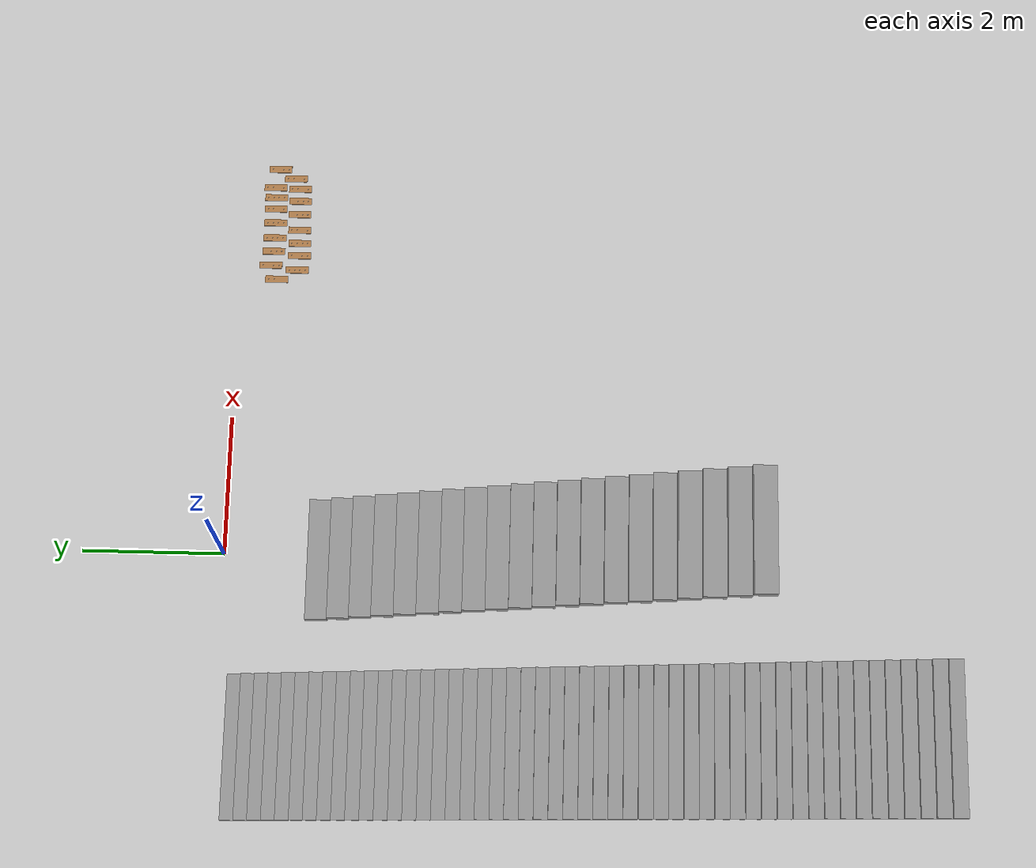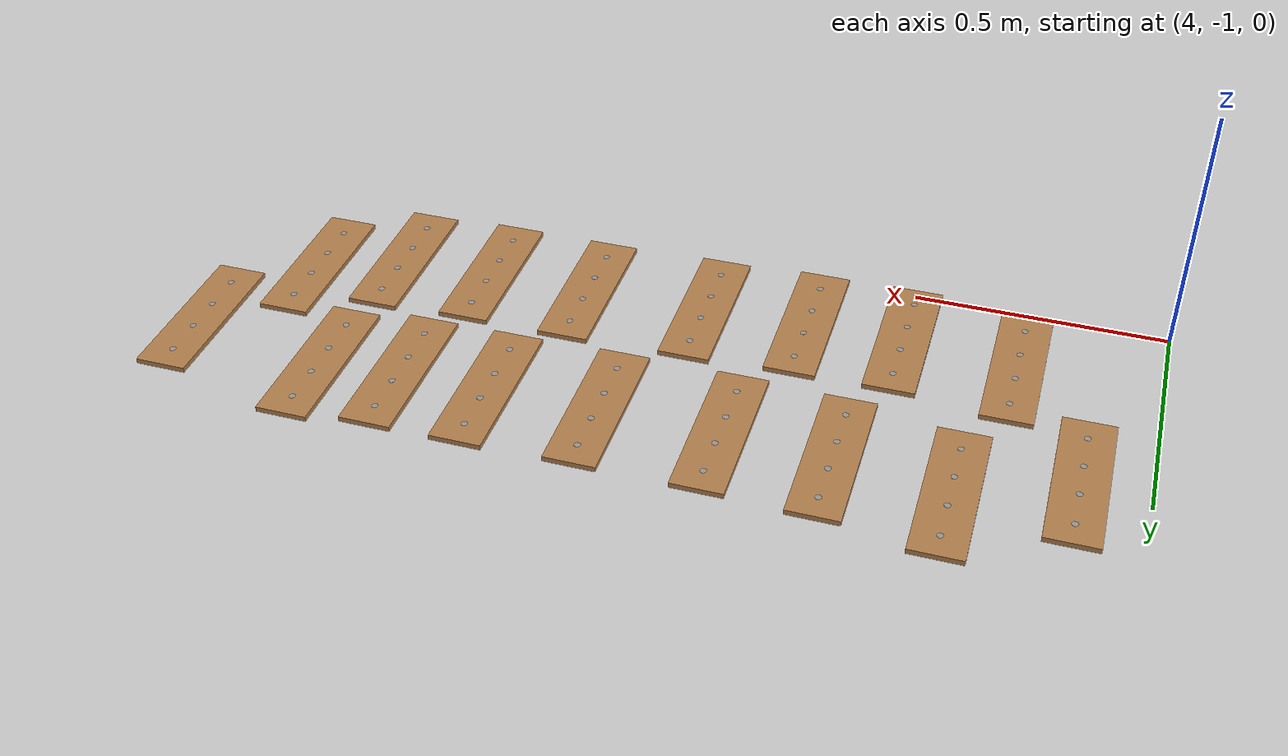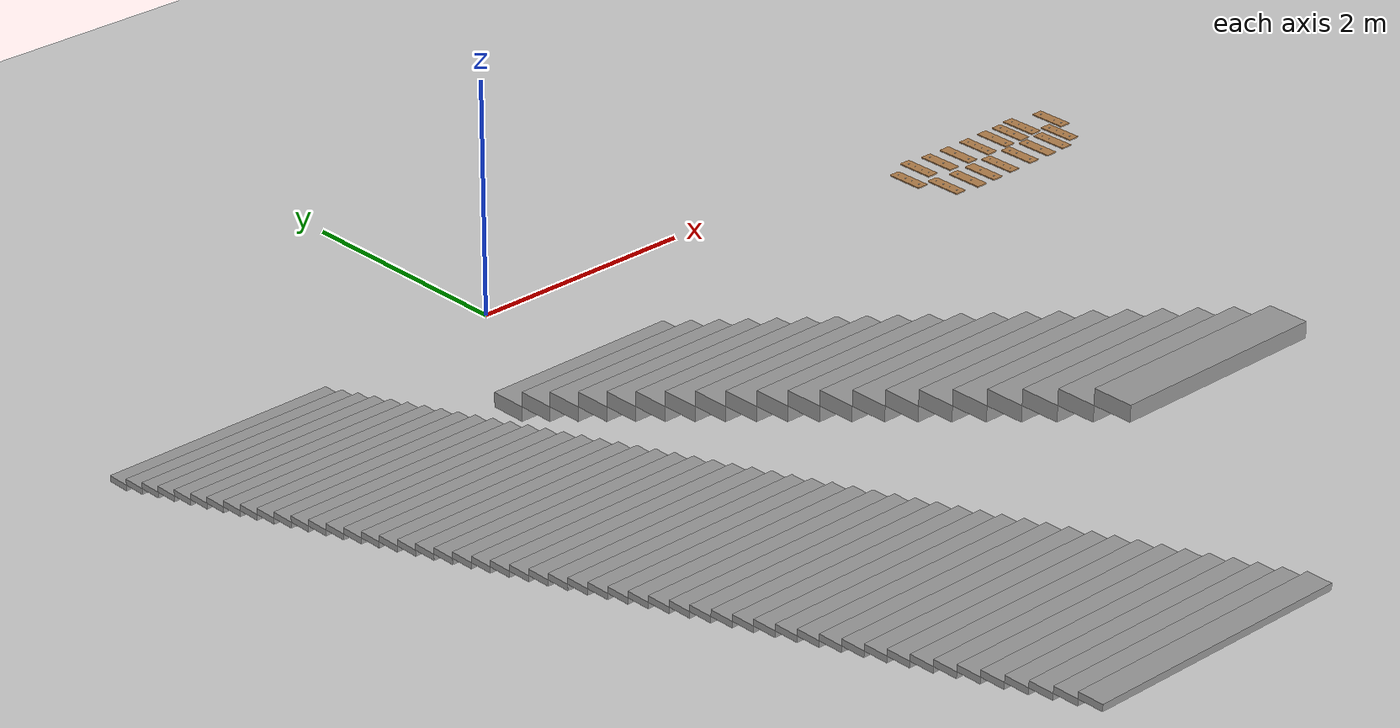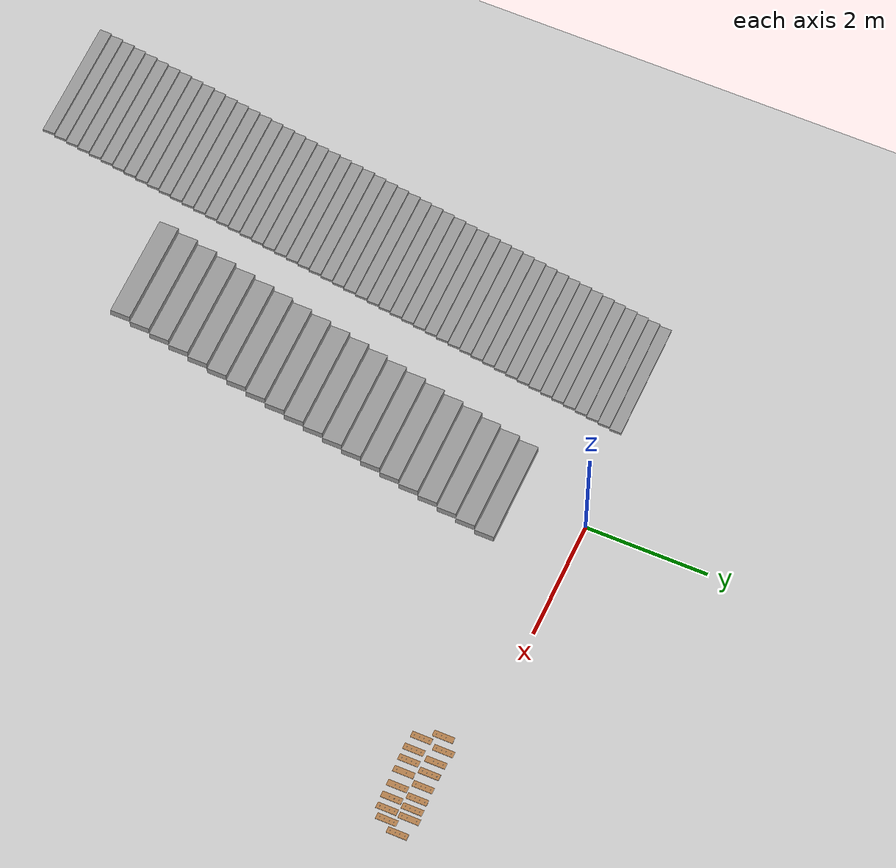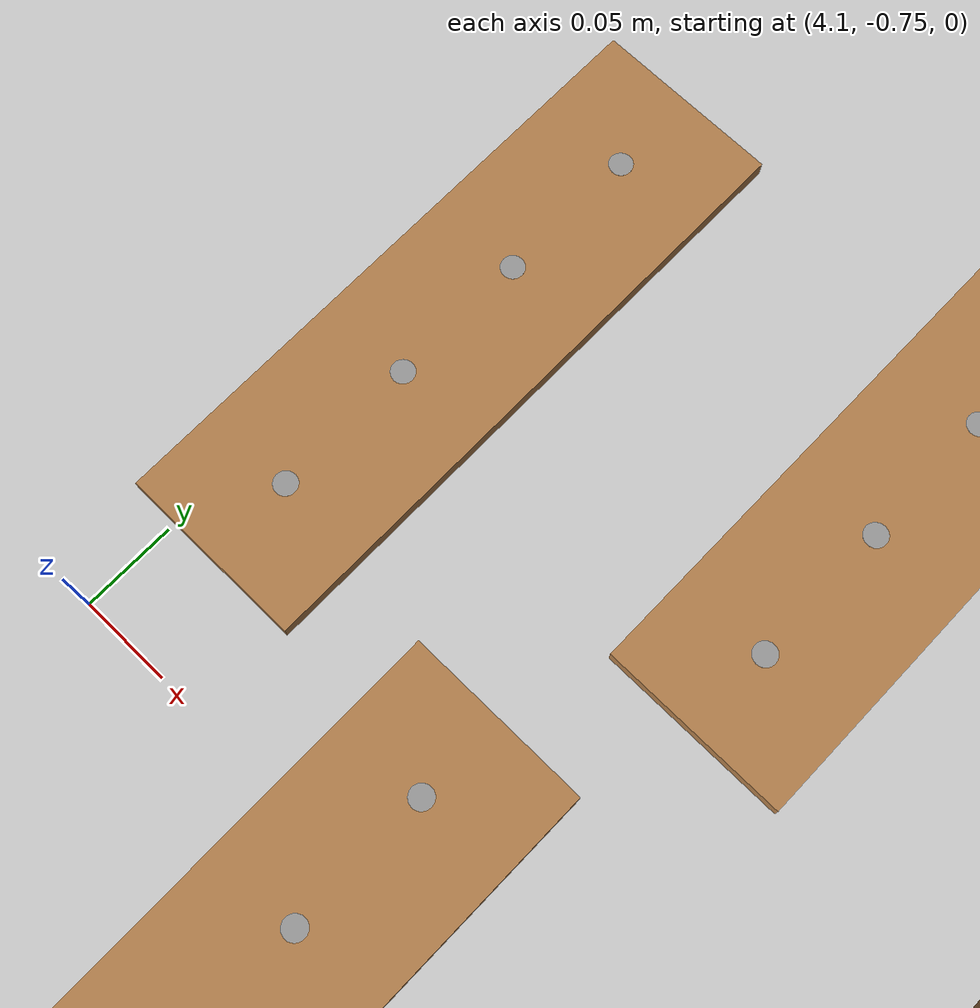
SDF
<sdf version="1.6">
 <world name="default">
  <light name="sun" type="directional">
   <pose>0 0 10 0 -0 0</pose>
   <diffuse>0.8 0.8 0.8 1</diffuse>
   <specular>0.2 0.2 0.2 1</specular>
   <attenuation>
    <range>1000</range>
    <constant>0.9</constant>
    <linear>0.01</linear>
    <quadratic>0.001</quadratic>
   </attenuation>
   <direction>-0.5 0.1 -0.9</direction>
  </light>
  <model name="ground_plane">
   <static>1</static>
   <link name="link">
    <collision name="collision">
     <geometry><plane><normal>0 0 1</normal><size>100 100</size></plane></geometry>
     <surface><friction><ode><mu>100</mu><mu2>50</mu2></ode></friction></surface>
    </collision>
    <visual name="visual">
     <cast_shadows>0</cast_shadows>
     <geometry><plane><normal>0 0 1</normal><size>100 100</size></plane></geometry>
     <material>
      <script><uri>file://media/materials/scripts/gazebo.material</uri><name>Gazebo/Grey</name></script>
     </material>
    </visual>
   </link>
  </model>
  <gravity>0 0 -9.8</gravity>
  <magnetic_field>6e-06 2.3e-05 -4.2e-05</magnetic_field>
  <atmosphere type="adiabatic"/>
  <physics name="default_physics" default="0" type="ode">
   <max_step_size>0.001</max_step_size>
   <real_time_factor>1</real_time_factor>
   <real_time_update_rate>1000</real_time_update_rate>
  </physics>
  <scene><ambient>0.4 0.4 0.4 1</ambient><background>0.7 0.7 0.7 1</background><shadows>1</shadows></scene>
  <audio><device>default</device></audio>
  <spherical_coordinates>
   <surface_model>EARTH_WGS84</surface_model>
   <latitude_deg>0</latitude_deg>
   <longitude_deg>0</longitude_deg>
   <elevation>0</elevation>
   <heading_deg>0</heading_deg>
  </spherical_coordinates>
  <model name="stair_short">
   <pose>-2.72 -4.97 0 0 -0 0</pose>
   <link name="Stairs_1">
    <visual name="Stairs_1_Visual_0">
     <pose>0 4.7383 0.025 0 -0 0</pose>
     <geometry><box><size>2.02 0.1934 0.05</size></box></geometry>
     <material>
      <script><uri>file://media/materials/scripts/gazebo.material</uri><name>Gazebo/Grey</name></script>
      <ambient>1 1 1 1</ambient>
     </material>
     <meta><layer>0</layer></meta>
    </visual>
    <collision name="Stairs_1_Collision_0">
     <geometry><box><size>2.02 0.1934 0.05</size></box></geometry>
     <pose>0 4.7383 0.025 0 -0 0</pose>
    </collision>
    <visual name="Stairs_1_Visual_1">
     <pose>0 4.5449 0.075 0 -0 0</pose>
     <geometry><box><size>2.02 0.1934 0.05</size></box></geometry>
     <material>
      <script><uri>file://media/materials/scripts/gazebo.material</uri><name>Gazebo/Grey</name></script>
      <ambient>1 1 1 1</ambient>
     </material>
     <meta><layer>0</layer></meta>
    </visual>
    <collision name="Stairs_1_Collision_1">
     <geometry><box><size>2.02 0.1934 0.05</size></box></geometry>
     <pose>0 4.5449 0.075 0 -0 0</pose>
    </collision>
    <visual name="Stairs_1_Visual_2">
     <pose>0 4.3515 0.125 0 -0 0</pose>
     <geometry><box><size>2.02 0.1934 0.05</size></box></geometry>
     <material>
      <script><uri>file://media/materials/scripts/gazebo.material</uri><name>Gazebo/Grey</name></script>
      <ambient>1 1 1 1</ambient>
     </material>
     <meta><layer>0</layer></meta>
    </visual>
    <collision name="Stairs_1_Collision_2">
     <geometry><box><size>2.02 0.1934 0.05</size></box></geometry>
     <pose>0 4.3515 0.125 0 -0 0</pose>
    </collision>
    <visual name="Stairs_1_Visual_3">
     <pose>0 4.1581 0.175 0 -0 0</pose>
     <geometry><box><size>2.02 0.1934 0.05</size></box></geometry>
     <material>
      <script><uri>file://media/materials/scripts/gazebo.material</uri><name>Gazebo/Grey</name></script>
      <ambient>1 1 1 1</ambient>
     </material>
     <meta><layer>0</layer></meta>
    </visual>
    <collision name="Stairs_1_Collision_3">
     <geometry><box><size>2.02 0.1934 0.05</size></box></geometry>
     <pose>0 4.1581 0.175 0 -0 0</pose>
    </collision>
    <visual name="Stairs_1_Visual_4">
     <pose>0 3.9647 0.225 0 -0 0</pose>
     <geometry><box><size>2.02 0.1934 0.05</size></box></geometry>
     <material>
      <script><uri>file://media/materials/scripts/gazebo.material</uri><name>Gazebo/Grey</name></script>
      <ambient>1 1 1 1</ambient>
     </material>
     <meta><layer>0</layer></meta>
    </visual>
    <collision name="Stairs_1_Collision_4">
     <geometry><box><size>2.02 0.1934 0.05</size></box></geometry>
     <pose>0 3.9647 0.225 0 -0 0</pose>
    </collision>
    <visual name="Stairs_1_Visual_5">
     <pose>0 3.7713 0.275 0 -0 0</pose>
     <geometry><box><size>2.02 0.1934 0.05</size></box></geometry>
     <material>
      <script><uri>file://media/materials/scripts/gazebo.material</uri><name>Gazebo/Grey</name></script>
      <ambient>1 1 1 1</ambient>
     </material>
     <meta><layer>0</layer></meta>
    </visual>
    <collision name="Stairs_1_Collision_5">
     <geometry><box><size>2.02 0.1934 0.05</size></box></geometry>
     <pose>0 3.7713 0.275 0 -0 0</pose>
    </collision>
    <visual name="Stairs_1_Visual_6">
     <pose>0 3.5779 0.325 0 -0 0</pose>
     <geometry><box><size>2.02 0.1934 0.05</size></box></geometry>
     <material>
      <script><uri>file://media/materials/scripts/gazebo.material</uri><name>Gazebo/Grey</name></script>
      <ambient>1 1 1 1</ambient>
     </material>
     <meta><layer>0</layer></meta>
    </visual>
    <collision name="Stairs_1_Collision_6">
     <geometry><box><size>2.02 0.1934 0.05</size></box></geometry>
     <pose>0 3.5779 0.325 0 -0 0</pose>
    </collision>
    <visual name="Stairs_1_Visual_7">
     <pose>0 3.3845 0.375 0 -0 0</pose>
     <geometry><box><size>2.02 0.1934 0.05</size></box></geometry>
     <material>
      <script><uri>file://media/materials/scripts/gazebo.material</uri><name>Gazebo/Grey</name></script>
      <ambient>1 1 1 1</ambient>
     </material>
     <meta><layer>0</layer></meta>
    </visual>
    <collision name="Stairs_1_Collision_7">
     <geometry><box><size>2.02 0.1934 0.05</size></box></geometry>
     <pose>0 3.3845 0.375 0 -0 0</pose>
    </collision>
    <visual name="Stairs_1_Visual_8">
     <pose>0 3.1911 0.425 0 -0 0</pose>
     <geometry><box><size>2.02 0.1934 0.05</size></box></geometry>
     <material>
      <script><uri>file://media/materials/scripts/gazebo.material</uri><name>Gazebo/Grey</name></script>
      <ambient>1 1 1 1</ambient>
     </material>
     <meta><layer>0</layer></meta>
    </visual>
    <collision name="Stairs_1_Collision_8">
     <geometry><box><size>2.02 0.1934 0.05</size></box></geometry>
     <pose>0 3.1911 0.425 0 -0 0</pose>
    </collision>
    <visual name="Stairs_1_Visual_9">
     <pose>0 2.9977 0.475 0 -0 0</pose>
     <geometry><box><size>2.02 0.1934 0.05</size></box></geometry>
     <material>
      <script><uri>file://media/materials/scripts/gazebo.material</uri><name>Gazebo/Grey</name></script>
      <ambient>1 1 1 1</ambient>
     </material>
     <meta><layer>0</layer></meta>
    </visual>
    <collision name="Stairs_1_Collision_9">
     <geometry><box><size>2.02 0.1934 0.05</size></box></geometry>
     <pose>0 2.9977 0.475 0 -0 0</pose>
    </collision>
    <visual name="Stairs_1_Visual_10">
     <pose>0 2.8043 0.525 0 -0 0</pose>
     <geometry><box><size>2.02 0.1934 0.05</size></box></geometry>
     <material>
      <script><uri>file://media/materials/scripts/gazebo.material</uri><name>Gazebo/Grey</name></script>
      <ambient>1 1 1 1</ambient>
     </material>
     <meta><layer>0</layer></meta>
    </visual>
    <collision name="Stairs_1_Collision_10">
     <geometry><box><size>2.02 0.1934 0.05</size></box></geometry>
     <pose>0 2.8043 0.525 0 -0 0</pose>
    </collision>
    <visual name="Stairs_1_Visual_11">
     <pose>0 2.6109 0.575 0 -0 0</pose>
     <geometry><box><size>2.02 0.1934 0.05</size></box></geometry>
     <material>
      <script><uri>file://media/materials/scripts/gazebo.material</uri><name>Gazebo/Grey</name></script>
      <ambient>1 1 1 1</ambient>
     </material>
     <meta><layer>0</layer></meta>
    </visual>
    <collision name="Stairs_1_Collision_11">
     <geometry><box><size>2.02 0.1934 0.05</size></box></geometry>
     <pose>0 2.6109 0.575 0 -0 0</pose>
    </collision>
    <visual name="Stairs_1_Visual_12">
     <pose>0 2.4175 0.625 0 -0 0</pose>
     <geometry><box><size>2.02 0.1934 0.05</size></box></geometry>
     <material>
      <script><uri>file://media/materials/scripts/gazebo.material</uri><name>Gazebo/Grey</name></script>
      <ambient>1 1 1 1</ambient>
     </material>
     <meta><layer>0</layer></meta>
    </visual>
    <collision name="Stairs_1_Collision_12">
     <geometry><box><size>2.02 0.1934 0.05</size></box></geometry>
     <pose>0 2.4175 0.625 0 -0 0</pose>
    </collision>
    <visual name="Stairs_1_Visual_13">
     <pose>0 2.2241 0.675 0 -0 0</pose>
     <geometry><box><size>2.02 0.1934 0.05</size></box></geometry>
     <material>
      <script><uri>file://media/materials/scripts/gazebo.material</uri><name>Gazebo/Grey</name></script>
      <ambient>1 1 1 1</ambient>
     </material>
     <meta><layer>0</layer></meta>
    </visual>
    <collision name="Stairs_1_Collision_13">
     <geometry><box><size>2.02 0.1934 0.05</size></box></geometry>
     <pose>0 2.2241 0.675 0 -0 0</pose>
    </collision>
    <visual name="Stairs_1_Visual_14">
     <pose>0 2.0307 0.725 0 -0 0</pose>
     <geometry><box><size>2.02 0.1934 0.05</size></box></geometry>
     <material>
      <script><uri>file://media/materials/scripts/gazebo.material</uri><name>Gazebo/Grey</name></script>
      <ambient>1 1 1 1</ambient>
     </material>
     <meta><layer>0</layer></meta>
    </visual>
    <collision name="Stairs_1_Collision_14">
     <geometry><box><size>2.02 0.1934 0.05</size></box></geometry>
     <pose>0 2.0307 0.725 0 -0 0</pose>
    </collision>
    <visual name="Stairs_1_Visual_15">
     <pose>0 1.8373 0.775 0 -0 0</pose>
     <geometry><box><size>2.02 0.1934 0.05</size></box></geometry>
     <material>
      <script><uri>file://media/materials/scripts/gazebo.material</uri><name>Gazebo/Grey</name></script>
      <ambient>1 1 1 1</ambient>
     </material>
     <meta><layer>0</layer></meta>
    </visual>
    <collision name="Stairs_1_Collision_15">
     <geometry><box><size>2.02 0.1934 0.05</size></box></geometry>
     <pose>0 1.8373 0.775 0 -0 0</pose>
    </collision>
    <visual name="Stairs_1_Visual_16">
     <pose>0 1.6439 0.825 0 -0 0</pose>
     <geometry><box><size>2.02 0.1934 0.05</size></box></geometry>
     <material>
      <script><uri>file://media/materials/scripts/gazebo.material</uri><name>Gazebo/Grey</name></script>
      <ambient>1 1 1 1</ambient>
     </material>
     <meta><layer>0</layer></meta>
    </visual>
    <collision name="Stairs_1_Collision_16">
     <geometry><box><size>2.02 0.1934 0.05</size></box></geometry>
     <pose>0 1.6439 0.825 0 -0 0</pose>
    </collision>
    <visual name="Stairs_1_Visual_17">
     <pose>0 1.4505 0.875 0 -0 0</pose>
     <geometry><box><size>2.02 0.1934 0.05</size></box></geometry>
     <material>
      <script><uri>file://media/materials/scripts/gazebo.material</uri><name>Gazebo/Grey</name></script>
      <ambient>1 1 1 1</ambient>
     </material>
     <meta><layer>0</layer></meta>
    </visual>
    <collision name="Stairs_1_Collision_17">
     <geometry><box><size>2.02 0.1934 0.05</size></box></geometry>
     <pose>0 1.4505 0.875 0 -0 0</pose>
    </collision>
    <visual name="Stairs_1_Visual_18">
     <pose>0 1.2571 0.925 0 -0 0</pose>
     <geometry><box><size>2.02 0.1934 0.05</size></box></geometry>
     <material>
      <script><uri>file://media/materials/scripts/gazebo.material</uri><name>Gazebo/Grey</name></script>
      <ambient>1 1 1 1</ambient>
     </material>
     <meta><layer>0</layer></meta>
    </visual>
    <collision name="Stairs_1_Collision_18">
     <geometry><box><size>2.02 0.1934 0.05</size></box></geometry>
     <pose>0 1.2571 0.925 0 -0 0</pose>
    </collision>
    <visual name="Stairs_1_Visual_19">
     <pose>0 1.0637 0.975 0 -0 0</pose>
     <geometry><box><size>2.02 0.1934 0.05</size></box></geometry>
     <material>
      <script><uri>file://media/materials/scripts/gazebo.material</uri><name>Gazebo/Grey</name></script>
      <ambient>1 1 1 1</ambient>
     </material>
     <meta><layer>0</layer></meta>
    </visual>
    <collision name="Stairs_1_Collision_19">
     <geometry><box><size>2.02 0.1934 0.05</size></box></geometry>
     <pose>0 1.0637 0.975 0 -0 0</pose>
    </collision>
    <visual name="Stairs_1_Visual_20">
     <pose>0 0.870299 1.025 0 -0 0</pose>
     <geometry><box><size>2.02 0.1934 0.05</size></box></geometry>
     <material>
      <script><uri>file://media/materials/scripts/gazebo.material</uri><name>Gazebo/Grey</name></script>
      <ambient>1 1 1 1</ambient>
     </material>
     <meta><layer>0</layer></meta>
    </visual>
    <collision name="Stairs_1_Collision_20">
     <geometry><box><size>2.02 0.1934 0.05</size></box></geometry>
     <pose>0 0.870299 1.025 0 -0 0</pose>
    </collision>
    <visual name="Stairs_1_Visual_21">
     <pose>0 0.6769 1.075 0 -0 0</pose>
     <geometry><box><size>2.02 0.1934 0.05</size></box></geometry>
     <material>
      <script><uri>file://media/materials/scripts/gazebo.material</uri><name>Gazebo/Grey</name></script>
      <ambient>1 1 1 1</ambient>
     </material>
     <meta><layer>0</layer></meta>
    </visual>
    <collision name="Stairs_1_Collision_21">
     <geometry><box><size>2.02 0.1934 0.05</size></box></geometry>
     <pose>0 0.6769 1.075 0 -0 0</pose>
    </collision>
    <visual name="Stairs_1_Visual_22">
     <pose>0 0.4835 1.125 0 -0 0</pose>
     <geometry><box><size>2.02 0.1934 0.05</size></box></geometry>
     <material>
      <script><uri>file://media/materials/scripts/gazebo.material</uri><name>Gazebo/Grey</name></script>
      <ambient>1 1 1 1</ambient>
     </material>
     <meta><layer>0</layer></meta>
    </visual>
    <collision name="Stairs_1_Collision_22">
     <geometry><box><size>2.02 0.1934 0.05</size></box></geometry>
     <pose>0 0.4835 1.125 0 -0 0</pose>
    </collision>
    <visual name="Stairs_1_Visual_23">
     <pose>0 0.2901 1.175 0 -0 0</pose>
     <geometry><box><size>2.02 0.1934 0.05</size></box></geometry>
     <material>
      <script><uri>file://media/materials/scripts/gazebo.material</uri><name>Gazebo/Grey</name></script>
      <ambient>1 1 1 1</ambient>
     </material>
     <meta><layer>0</layer></meta>
    </visual>
    <collision name="Stairs_1_Collision_23">
     <geometry><box><size>2.02 0.1934 0.05</size></box></geometry>
     <pose>0 0.2901 1.175 0 -0 0</pose>
    </collision>
    <visual name="Stairs_1_Visual_24">
     <pose>0 0.0967 1.225 0 -0 0</pose>
     <geometry><box><size>2.02 0.1934 0.05</size></box></geometry>
     <material>
      <script><uri>file://media/materials/scripts/gazebo.material</uri><name>Gazebo/Grey</name></script>
      <ambient>1 1 1 1</ambient>
     </material>
     <meta><layer>0</layer></meta>
    </visual>
    <collision name="Stairs_1_Collision_24">
     <geometry><box><size>2.02 0.1934 0.05</size></box></geometry>
     <pose>0 0.0967 1.225 0 -0 0</pose>
    </collision>
    <visual name="Stairs_1_Visual_25">
     <pose>0 -0.096701 1.275 0 -0 0</pose>
     <geometry><box><size>2.02 0.1934 0.05</size></box></geometry>
     <material>
      <script><uri>file://media/materials/scripts/gazebo.material</uri><name>Gazebo/Grey</name></script>
      <ambient>1 1 1 1</ambient>
     </material>
     <meta><layer>0</layer></meta>
    </visual>
    <collision name="Stairs_1_Collision_25">
     <geometry><box><size>2.02 0.1934 0.05</size></box></geometry>
     <pose>0 -0.096701 1.275 0 -0 0</pose>
    </collision>
    <visual name="Stairs_1_Visual_26">
     <pose>0 -0.2901 1.325 0 -0 0</pose>
     <geometry><box><size>2.02 0.1934 0.05</size></box></geometry>
     <material>
      <script><uri>file://media/materials/scripts/gazebo.material</uri><name>Gazebo/Grey</name></script>
      <ambient>1 1 1 1</ambient>
     </material>
     <meta><layer>0</layer></meta>
    </visual>
    <collision name="Stairs_1_Collision_26">
     <geometry><box><size>2.02 0.1934 0.05</size></box></geometry>
     <pose>0 -0.2901 1.325 0 -0 0</pose>
    </collision>
    <visual name="Stairs_1_Visual_27">
     <pose>0 -0.4835 1.375 0 -0 0</pose>
     <geometry><box><size>2.02 0.1934 0.05</size></box></geometry>
     <material>
      <script><uri>file://media/materials/scripts/gazebo.material</uri><name>Gazebo/Grey</name></script>
      <ambient>1 1 1 1</ambient>
     </material>
     <meta><layer>0</layer></meta>
    </visual>
    <collision name="Stairs_1_Collision_27">
     <geometry><box><size>2.02 0.1934 0.05</size></box></geometry>
     <pose>0 -0.4835 1.375 0 -0 0</pose>
    </collision>
    <visual name="Stairs_1_Visual_28">
     <pose>0 -0.6769 1.425 0 -0 0</pose>
     <geometry><box><size>2.02 0.1934 0.05</size></box></geometry>
     <material>
      <script><uri>file://media/materials/scripts/gazebo.material</uri><name>Gazebo/Grey</name></script>
      <ambient>1 1 1 1</ambient>
     </material>
     <meta><layer>0</layer></meta>
    </visual>
    <collision name="Stairs_1_Collision_28">
     <geometry><box><size>2.02 0.1934 0.05</size></box></geometry>
     <pose>0 -0.6769 1.425 0 -0 0</pose>
    </collision>
    <visual name="Stairs_1_Visual_29">
     <pose>0 -0.8703 1.475 0 -0 0</pose>
     <geometry><box><size>2.02 0.1934 0.05</size></box></geometry>
     <material>
      <script><uri>file://media/materials/scripts/gazebo.material</uri><name>Gazebo/Grey</name></script>
      <ambient>1 1 1 1</ambient>
     </material>
     <meta><layer>0</layer></meta>
    </visual>
    <collision name="Stairs_1_Collision_29">
     <geometry><box><size>2.02 0.1934 0.05</size></box></geometry>
     <pose>0 -0.8703 1.475 0 -0 0</pose>
    </collision>
    <visual name="Stairs_1_Visual_30">
     <pose>0 -1.0637 1.525 0 -0 0</pose>
     <geometry><box><size>2.02 0.1934 0.05</size></box></geometry>
     <material>
      <script><uri>file://media/materials/scripts/gazebo.material</uri><name>Gazebo/Grey</name></script>
      <ambient>1 1 1 1</ambient>
     </material>
     <meta><layer>0</layer></meta>
    </visual>
    <collision name="Stairs_1_Collision_30">
     <geometry><box><size>2.02 0.1934 0.05</size></box></geometry>
     <pose>0 -1.0637 1.525 0 -0 0</pose>
    </collision>
    <visual name="Stairs_1_Visual_31">
     <pose>0 -1.2571 1.575 0 -0 0</pose>
     <geometry><box><size>2.02 0.1934 0.05</size></box></geometry>
     <material>
      <script><uri>file://media/materials/scripts/gazebo.material</uri><name>Gazebo/Grey</name></script>
      <ambient>1 1 1 1</ambient>
     </material>
     <meta><layer>0</layer></meta>
    </visual>
    <collision name="Stairs_1_Collision_31">
     <geometry><box><size>2.02 0.1934 0.05</size></box></geometry>
     <pose>0 -1.2571 1.575 0 -0 0</pose>
    </collision>
    <visual name="Stairs_1_Visual_32">
     <pose>0 -1.4505 1.625 0 -0 0</pose>
     <geometry><box><size>2.02 0.1934 0.05</size></box></geometry>
     <material>
      <script><uri>file://media/materials/scripts/gazebo.material</uri><name>Gazebo/Grey</name></script>
      <ambient>1 1 1 1</ambient>
     </material>
     <meta><layer>0</layer></meta>
    </visual>
    <collision name="Stairs_1_Collision_32">
     <geometry><box><size>2.02 0.1934 0.05</size></box></geometry>
     <pose>0 -1.4505 1.625 0 -0 0</pose>
    </collision>
    <visual name="Stairs_1_Visual_33">
     <pose>0 -1.6439 1.675 0 -0 0</pose>
     <geometry><box><size>2.02 0.1934 0.05</size></box></geometry>
     <material>
      <script><uri>file://media/materials/scripts/gazebo.material</uri><name>Gazebo/Grey</name></script>
      <ambient>1 1 1 1</ambient>
     </material>
     <meta><layer>0</layer></meta>
    </visual>
    <collision name="Stairs_1_Collision_33">
     <geometry><box><size>2.02 0.1934 0.05</size></box></geometry>
     <pose>0 -1.6439 1.675 0 -0 0</pose>
    </collision>
    <visual name="Stairs_1_Visual_34">
     <pose>0 -1.8373 1.725 0 -0 0</pose>
     <geometry><box><size>2.02 0.1934 0.05</size></box></geometry>
     <material>
      <script><uri>file://media/materials/scripts/gazebo.material</uri><name>Gazebo/Grey</name></script>
      <ambient>1 1 1 1</ambient>
     </material>
     <meta><layer>0</layer></meta>
    </visual>
    <collision name="Stairs_1_Collision_34">
     <geometry><box><size>2.02 0.1934 0.05</size></box></geometry>
     <pose>0 -1.8373 1.725 0 -0 0</pose>
    </collision>
    <visual name="Stairs_1_Visual_35">
     <pose>0 -2.0307 1.775 0 -0 0</pose>
     <geometry><box><size>2.02 0.1934 0.05</size></box></geometry>
     <material>
      <script><uri>file://media/materials/scripts/gazebo.material</uri><name>Gazebo/Grey</name></script>
      <ambient>1 1 1 1</ambient>
     </material>
     <meta><layer>0</layer></meta>
    </visual>
    <collision name="Stairs_1_Collision_35">
     <geometry><box><size>2.02 0.1934 0.05</size></box></geometry>
     <pose>0 -2.0307 1.775 0 -0 0</pose>
    </collision>
    <visual name="Stairs_1_Visual_36">
     <pose>0 -2.2241 1.825 0 -0 0</pose>
     <geometry><box><size>2.02 0.1934 0.05</size></box></geometry>
     <material>
      <script><uri>file://media/materials/scripts/gazebo.material</uri><name>Gazebo/Grey</name></script>
      <ambient>1 1 1 1</ambient>
     </material>
     <meta><layer>0</layer></meta>
    </visual>
    <collision name="Stairs_1_Collision_36">
     <geometry><box><size>2.02 0.1934 0.05</size></box></geometry>
     <pose>0 -2.2241 1.825 0 -0 0</pose>
    </collision>
    <visual name="Stairs_1_Visual_37">
     <pose>0 -2.4175 1.875 0 -0 0</pose>
     <geometry><box><size>2.02 0.1934 0.05</size></box></geometry>
     <material>
      <script><uri>file://media/materials/scripts/gazebo.material</uri><name>Gazebo/Grey</name></script>
      <ambient>1 1 1 1</ambient>
     </material>
     <meta><layer>0</layer></meta>
    </visual>
    <collision name="Stairs_1_Collision_37">
     <geometry><box><size>2.02 0.1934 0.05</size></box></geometry>
     <pose>0 -2.4175 1.875 0 -0 0</pose>
    </collision>
    <visual name="Stairs_1_Visual_38">
     <pose>0 -2.6109 1.925 0 -0 0</pose>
     <geometry><box><size>2.02 0.1934 0.05</size></box></geometry>
     <material>
      <script><uri>file://media/materials/scripts/gazebo.material</uri><name>Gazebo/Grey</name></script>
      <ambient>1 1 1 1</ambient>
     </material>
     <meta><layer>0</layer></meta>
    </visual>
    <collision name="Stairs_1_Collision_38">
     <geometry><box><size>2.02 0.1934 0.05</size></box></geometry>
     <pose>0 -2.6109 1.925 0 -0 0</pose>
    </collision>
    <visual name="Stairs_1_Visual_39">
     <pose>0 -2.8043 1.975 0 -0 0</pose>
     <geometry><box><size>2.02 0.1934 0.05</size></box></geometry>
     <material>
      <script><uri>file://media/materials/scripts/gazebo.material</uri><name>Gazebo/Grey</name></script>
      <ambient>1 1 1 1</ambient>
     </material>
     <meta><layer>0</layer></meta>
    </visual>
    <collision name="Stairs_1_Collision_39">
     <geometry><box><size>2.02 0.1934 0.05</size></box></geometry>
     <pose>0 -2.8043 1.975 0 -0 0</pose>
    </collision>
    <visual name="Stairs_1_Visual_40">
     <pose>0 -2.9977 2.025 0 -0 0</pose>
     <geometry><box><size>2.02 0.1934 0.05</size></box></geometry>
     <material>
      <script><uri>file://media/materials/scripts/gazebo.material</uri><name>Gazebo/Grey</name></script>
      <ambient>1 1 1 1</ambient>
     </material>
     <meta><layer>0</layer></meta>
    </visual>
    <collision name="Stairs_1_Collision_40">
     <geometry><box><size>2.02 0.1934 0.05</size></box></geometry>
     <pose>0 -2.9977 2.025 0 -0 0</pose>
    </collision>
    <visual name="Stairs_1_Visual_41">
     <pose>0 -3.1911 2.075 0 -0 0</pose>
     <geometry><box><size>2.02 0.1934 0.05</size></box></geometry>
     <material>
      <script><uri>file://media/materials/scripts/gazebo.material</uri><name>Gazebo/Grey</name></script>
      <ambient>1 1 1 1</ambient>
     </material>
     <meta><layer>0</layer></meta>
    </visual>
    <collision name="Stairs_1_Collision_41">
     <geometry><box><size>2.02 0.1934 0.05</size></box></geometry>
     <pose>0 -3.1911 2.075 0 -0 0</pose>
    </collision>
    <visual name="Stairs_1_Visual_42">
     <pose>0 -3.3845 2.125 0 -0 0</pose>
     <geometry><box><size>2.02 0.1934 0.05</size></box></geometry>
     <material>
      <script><uri>file://media/materials/scripts/gazebo.material</uri><name>Gazebo/Grey</name></script>
      <ambient>1 1 1 1</ambient>
     </material>
     <meta><layer>0</layer></meta>
    </visual>
    <collision name="Stairs_1_Collision_42">
     <geometry><box><size>2.02 0.1934 0.05</size></box></geometry>
     <pose>0 -3.3845 2.125 0 -0 0</pose>
    </collision>
    <visual name="Stairs_1_Visual_43">
     <pose>0 -3.5779 2.175 0 -0 0</pose>
     <geometry><box><size>2.02 0.1934 0.05</size></box></geometry>
     <material>
      <script><uri>file://media/materials/scripts/gazebo.material</uri><name>Gazebo/Grey</name></script>
      <ambient>1 1 1 1</ambient>
     </material>
     <meta><layer>0</layer></meta>
    </visual>
    <collision name="Stairs_1_Collision_43">
     <geometry><box><size>2.02 0.1934 0.05</size></box></geometry>
     <pose>0 -3.5779 2.175 0 -0 0</pose>
    </collision>
    <visual name="Stairs_1_Visual_44">
     <pose>0 -3.7713 2.225 0 -0 0</pose>
     <geometry><box><size>2.02 0.1934 0.05</size></box></geometry>
     <material>
      <script><uri>file://media/materials/scripts/gazebo.material</uri><name>Gazebo/Grey</name></script>
      <ambient>1 1 1 1</ambient>
     </material>
     <meta><layer>0</layer></meta>
    </visual>
    <collision name="Stairs_1_Collision_44">
     <geometry><box><size>2.02 0.1934 0.05</size></box></geometry>
     <pose>0 -3.7713 2.225 0 -0 0</pose>
    </collision>
    <visual name="Stairs_1_Visual_45">
     <pose>0 -3.9647 2.275 0 -0 0</pose>
     <geometry><box><size>2.02 0.1934 0.05</size></box></geometry>
     <material>
      <script><uri>file://media/materials/scripts/gazebo.material</uri><name>Gazebo/Grey</name></script>
      <ambient>1 1 1 1</ambient>
     </material>
     <meta><layer>0</layer></meta>
    </visual>
    <collision name="Stairs_1_Collision_45">
     <geometry><box><size>2.02 0.1934 0.05</size></box></geometry>
     <pose>0 -3.9647 2.275 0 -0 0</pose>
    </collision>
    <visual name="Stairs_1_Visual_46">
     <pose>0 -4.1581 2.325 0 -0 0</pose>
     <geometry><box><size>2.02 0.1934 0.05</size></box></geometry>
     <material>
      <script><uri>file://media/materials/scripts/gazebo.material</uri><name>Gazebo/Grey</name></script>
      <ambient>1 1 1 1</ambient>
     </material>
     <meta><layer>0</layer></meta>
    </visual>
    <collision name="Stairs_1_Collision_46">
     <geometry><box><size>2.02 0.1934 0.05</size></box></geometry>
     <pose>0 -4.1581 2.325 0 -0 0</pose>
    </collision>
    <visual name="Stairs_1_Visual_47">
     <pose>0 -4.3515 2.375 0 -0 0</pose>
     <geometry><box><size>2.02 0.1934 0.05</size></box></geometry>
     <material>
      <script><uri>file://media/materials/scripts/gazebo.material</uri><name>Gazebo/Grey</name></script>
      <ambient>1 1 1 1</ambient>
     </material>
     <meta><layer>0</layer></meta>
    </visual>
    <collision name="Stairs_1_Collision_47">
     <geometry><box><size>2.02 0.1934 0.05</size></box></geometry>
     <pose>0 -4.3515 2.375 0 -0 0</pose>
    </collision>
    <visual name="Stairs_1_Visual_48">
     <pose>0 -4.5449 2.425 0 -0 0</pose>
     <geometry><box><size>2.02 0.1934 0.05</size></box></geometry>
     <material>
      <script><uri>file://media/materials/scripts/gazebo.material</uri><name>Gazebo/Grey</name></script>
      <ambient>1 1 1 1</ambient>
     </material>
     <meta><layer>0</layer></meta>
    </visual>
    <collision name="Stairs_1_Collision_48">
     <geometry><box><size>2.02 0.1934 0.05</size></box></geometry>
     <pose>0 -4.5449 2.425 0 -0 0</pose>
    </collision>
    <visual name="Stairs_1_Visual_49">
     <pose>0 -4.7383 2.475 0 -0 0</pose>
     <geometry><box><size>2.02 0.1934 0.05</size></box></geometry>
     <material>
      <script><uri>file://media/materials/scripts/gazebo.material</uri><name>Gazebo/Grey</name></script>
      <ambient>1 1 1 1</ambient>
     </material>
     <meta><layer>0</layer></meta>
    </visual>
    <collision name="Stairs_1_Collision_49">
     <geometry><box><size>2.02 0.1934 0.05</size></box></geometry>
     <pose>0 -4.7383 2.475 0 -0 0</pose>
    </collision>
   </link>
   <static>1</static>
  </model>
  <model name="stair2">
   <pose>-0.07 -4.32 0 0 -0 0</pose>
   <link name="Stairs_1">
    <visual name="Stairs_1_Visual_0">
     <pose>-0 2.98775 0.0625 0 -0 0</pose>
     <geometry><box><size>1.72 0.3145 0.125</size></box></geometry>
     <material>
      <script><uri>file://media/materials/scripts/gazebo.material</uri><name>Gazebo/Grey</name></script>
      <ambient>1 1 1 1</ambient>
     </material>
     <meta><layer>0</layer></meta>
    </visual>
    <collision name="Stairs_1_Collision_0">
     <geometry><box><size>1.72 0.3145 0.125</size></box></geometry>
     <pose>-0 2.98775 0.0625 0 -0 0</pose>
    </collision>
    <visual name="Stairs_1_Visual_1">
     <pose>-0 2.67325 0.1875 0 -0 0</pose>
     <geometry><box><size>1.72 0.3145 0.125</size></box></geometry>
     <material>
      <script><uri>file://media/materials/scripts/gazebo.material</uri><name>Gazebo/Grey</name></script>
      <ambient>1 1 1 1</ambient>
     </material>
     <meta><layer>0</layer></meta>
    </visual>
    <collision name="Stairs_1_Collision_1">
     <geometry><box><size>1.72 0.3145 0.125</size></box></geometry>
     <pose>-0 2.67325 0.1875 0 -0 0</pose>
    </collision>
    <visual name="Stairs_1_Visual_2">
     <pose>-0 2.35875 0.3125 0 -0 0</pose>
     <geometry><box><size>1.72 0.3145 0.125</size></box></geometry>
     <material>
      <script><uri>file://media/materials/scripts/gazebo.material</uri><name>Gazebo/Grey</name></script>
      <ambient>1 1 1 1</ambient>
     </material>
     <meta><layer>0</layer></meta>
    </visual>
    <collision name="Stairs_1_Collision_2">
     <geometry><box><size>1.72 0.3145 0.125</size></box></geometry>
     <pose>-0 2.35875 0.3125 0 -0 0</pose>
    </collision>
    <visual name="Stairs_1_Visual_3">
     <pose>-0 2.04425 0.4375 0 -0 0</pose>
     <geometry><box><size>1.72 0.3145 0.125</size></box></geometry>
     <material>
      <script><uri>file://media/materials/scripts/gazebo.material</uri><name>Gazebo/Grey</name></script>
      <ambient>1 1 1 1</ambient>
     </material>
     <meta><layer>0</layer></meta>
    </visual>
    <collision name="Stairs_1_Collision_3">
     <geometry><box><size>1.72 0.3145 0.125</size></box></geometry>
     <pose>-0 2.04425 0.4375 0 -0 0</pose>
    </collision>
    <visual name="Stairs_1_Visual_4">
     <pose>-0 1.72975 0.5625 0 -0 0</pose>
     <geometry><box><size>1.72 0.3145 0.125</size></box></geometry>
     <material>
      <script><uri>file://media/materials/scripts/gazebo.material</uri><name>Gazebo/Grey</name></script>
      <ambient>1 1 1 1</ambient>
     </material>
     <meta><layer>0</layer></meta>
    </visual>
    <collision name="Stairs_1_Collision_4">
     <geometry><box><size>1.72 0.3145 0.125</size></box></geometry>
     <pose>-0 1.72975 0.5625 0 -0 0</pose>
    </collision>
    <visual name="Stairs_1_Visual_5">
     <pose>-0 1.41525 0.6875 0 -0 0</pose>
     <geometry><box><size>1.72 0.3145 0.125</size></box></geometry>
     <material>
      <script><uri>file://media/materials/scripts/gazebo.material</uri><name>Gazebo/Grey</name></script>
      <ambient>1 1 1 1</ambient>
     </material>
     <meta><layer>0</layer></meta>
    </visual>
    <collision name="Stairs_1_Collision_5">
     <geometry><box><size>1.72 0.3145 0.125</size></box></geometry>
     <pose>-0 1.41525 0.6875 0 -0 0</pose>
    </collision>
    <visual name="Stairs_1_Visual_6">
     <pose>-0 1.10075 0.8125 0 -0 0</pose>
     <geometry><box><size>1.72 0.3145 0.125</size></box></geometry>
     <material>
      <script><uri>file://media/materials/scripts/gazebo.material</uri><name>Gazebo/Grey</name></script>
      <ambient>1 1 1 1</ambient>
     </material>
     <meta><layer>0</layer></meta>
    </visual>
    <collision name="Stairs_1_Collision_6">
     <geometry><box><size>1.72 0.3145 0.125</size></box></geometry>
     <pose>-0 1.10075 0.8125 0 -0 0</pose>
    </collision>
    <visual name="Stairs_1_Visual_7">
     <pose>-0 0.78625 0.9375 0 -0 0</pose>
     <geometry><box><size>1.72 0.3145 0.125</size></box></geometry>
     <material>
      <script><uri>file://media/materials/scripts/gazebo.material</uri><name>Gazebo/Grey</name></script>
      <ambient>1 1 1 1</ambient>
     </material>
     <meta><layer>0</layer></meta>
    </visual>
    <collision name="Stairs_1_Collision_7">
     <geometry><box><size>1.72 0.3145 0.125</size></box></geometry>
     <pose>-0 0.78625 0.9375 0 -0 0</pose>
    </collision>
    <visual name="Stairs_1_Visual_8">
     <pose>-0 0.47175 1.0625 0 -0 0</pose>
     <geometry><box><size>1.72 0.3145 0.125</size></box></geometry>
     <material>
      <script><uri>file://media/materials/scripts/gazebo.material</uri><name>Gazebo/Grey</name></script>
      <ambient>1 1 1 1</ambient>
     </material>
     <meta><layer>0</layer></meta>
    </visual>
    <collision name="Stairs_1_Collision_8">
     <geometry><box><size>1.72 0.3145 0.125</size></box></geometry>
     <pose>-0 0.47175 1.0625 0 -0 0</pose>
    </collision>
    <visual name="Stairs_1_Visual_9">
     <pose>-0 0.15725 1.1875 0 -0 0</pose>
     <geometry><box><size>1.72 0.3145 0.125</size></box></geometry>
     <material>
      <script><uri>file://media/materials/scripts/gazebo.material</uri><name>Gazebo/Grey</name></script>
      <ambient>1 1 1 1</ambient>
     </material>
     <meta><layer>0</layer></meta>
    </visual>
    <collision name="Stairs_1_Collision_9">
     <geometry><box><size>1.72 0.3145 0.125</size></box></geometry>
     <pose>-0 0.15725 1.1875 0 -0 0</pose>
    </collision>
    <visual name="Stairs_1_Visual_10">
     <pose>-0 -0.15725 1.3125 0 -0 0</pose>
     <geometry><box><size>1.72 0.3145 0.125</size></box></geometry>
     <material>
      <script><uri>file://media/materials/scripts/gazebo.material</uri><name>Gazebo/Grey</name></script>
      <ambient>1 1 1 1</ambient>
     </material>
     <meta><layer>0</layer></meta>
    </visual>
    <collision name="Stairs_1_Collision_10">
     <geometry><box><size>1.72 0.3145 0.125</size></box></geometry>
     <pose>-0 -0.15725 1.3125 0 -0 0</pose>
    </collision>
    <visual name="Stairs_1_Visual_11">
     <pose>-0 -0.47175 1.4375 0 -0 0</pose>
     <geometry><box><size>1.72 0.3145 0.125</size></box></geometry>
     <material>
      <script><uri>file://media/materials/scripts/gazebo.material</uri><name>Gazebo/Grey</name></script>
      <ambient>1 1 1 1</ambient>
     </material>
     <meta><layer>0</layer></meta>
    </visual>
    <collision name="Stairs_1_Collision_11">
     <geometry><box><size>1.72 0.3145 0.125</size></box></geometry>
     <pose>-0 -0.47175 1.4375 0 -0 0</pose>
    </collision>
    <visual name="Stairs_1_Visual_12">
     <pose>-0 -0.78625 1.5625 0 -0 0</pose>
     <geometry><box><size>1.72 0.3145 0.125</size></box></geometry>
     <material>
      <script><uri>file://media/materials/scripts/gazebo.material</uri><name>Gazebo/Grey</name></script>
      <ambient>1 1 1 1</ambient>
     </material>
     <meta><layer>0</layer></meta>
    </visual>
    <collision name="Stairs_1_Collision_12">
     <geometry><box><size>1.72 0.3145 0.125</size></box></geometry>
     <pose>-0 -0.78625 1.5625 0 -0 0</pose>
    </collision>
    <visual name="Stairs_1_Visual_13">
     <pose>-0 -1.10075 1.6875 0 -0 0</pose>
     <geometry><box><size>1.72 0.3145 0.125</size></box></geometry>
     <material>
      <script><uri>file://media/materials/scripts/gazebo.material</uri><name>Gazebo/Grey</name></script>
      <ambient>1 1 1 1</ambient>
     </material>
     <meta><layer>0</layer></meta>
    </visual>
    <collision name="Stairs_1_Collision_13">
     <geometry><box><size>1.72 0.3145 0.125</size></box></geometry>
     <pose>-0 -1.10075 1.6875 0 -0 0</pose>
    </collision>
    <visual name="Stairs_1_Visual_14">
     <pose>-0 -1.41525 1.8125 0 -0 0</pose>
     <geometry><box><size>1.72 0.3145 0.125</size></box></geometry>
     <material>
      <script><uri>file://media/materials/scripts/gazebo.material</uri><name>Gazebo/Grey</name></script>
      <ambient>1 1 1 1</ambient>
     </material>
     <meta><layer>0</layer></meta>
    </visual>
    <collision name="Stairs_1_Collision_14">
     <geometry><box><size>1.72 0.3145 0.125</size></box></geometry>
     <pose>-0 -1.41525 1.8125 0 -0 0</pose>
    </collision>
    <visual name="Stairs_1_Visual_15">
     <pose>-0 -1.72975 1.9375 0 -0 0</pose>
     <geometry><box><size>1.72 0.3145 0.125</size></box></geometry>
     <material>
      <script><uri>file://media/materials/scripts/gazebo.material</uri><name>Gazebo/Grey</name></script>
      <ambient>1 1 1 1</ambient>
     </material>
     <meta><layer>0</layer></meta>
    </visual>
    <collision name="Stairs_1_Collision_15">
     <geometry><box><size>1.72 0.3145 0.125</size></box></geometry>
     <pose>-0 -1.72975 1.9375 0 -0 0</pose>
    </collision>
    <visual name="Stairs_1_Visual_16">
     <pose>-0 -2.04425 2.0625 0 -0 0</pose>
     <geometry><box><size>1.72 0.3145 0.125</size></box></geometry>
     <material>
      <script><uri>file://media/materials/scripts/gazebo.material</uri><name>Gazebo/Grey</name></script>
      <ambient>1 1 1 1</ambient>
     </material>
     <meta><layer>0</layer></meta>
    </visual>
    <collision name="Stairs_1_Collision_16">
     <geometry><box><size>1.72 0.3145 0.125</size></box></geometry>
     <pose>-0 -2.04425 2.0625 0 -0 0</pose>
    </collision>
    <visual name="Stairs_1_Visual_17">
     <pose>-0 -2.35875 2.1875 0 -0 0</pose>
     <geometry><box><size>1.72 0.3145 0.125</size></box></geometry>
     <material>
      <script><uri>file://media/materials/scripts/gazebo.material</uri><name>Gazebo/Grey</name></script>
      <ambient>1 1 1 1</ambient>
     </material>
     <meta><layer>0</layer></meta>
    </visual>
    <collision name="Stairs_1_Collision_17">
     <geometry><box><size>1.72 0.3145 0.125</size></box></geometry>
     <pose>-0 -2.35875 2.1875 0 -0 0</pose>
    </collision>
    <visual name="Stairs_1_Visual_18">
     <pose>-0 -2.67325 2.3125 0 -0 0</pose>
     <geometry><box><size>1.72 0.3145 0.125</size></box></geometry>
     <material>
      <script><uri>file://media/materials/scripts/gazebo.material</uri><name>Gazebo/Grey</name></script>
      <ambient>1 1 1 1</ambient>
     </material>
     <meta><layer>0</layer></meta>
    </visual>
    <collision name="Stairs_1_Collision_18">
     <geometry><box><size>1.72 0.3145 0.125</size></box></geometry>
     <pose>-0 -2.67325 2.3125 0 -0 0</pose>
    </collision>
    <visual name="Stairs_1_Visual_19">
     <pose>-0 -2.98775 2.4375 0 -0 0</pose>
     <geometry><box><size>1.72 0.3145 0.125</size></box></geometry>
     <material>
      <script><uri>file://media/materials/scripts/gazebo.material</uri><name>Gazebo/Grey</name></script>
      <ambient>1 1 1 1</ambient>
     </material>
     <meta><layer>0</layer></meta>
    </visual>
    <collision name="Stairs_1_Collision_19">
     <geometry><box><size>1.72 0.3145 0.125</size></box></geometry>
     <pose>-0 -2.98775 2.4375 0 -0 0</pose>
    </collision>
   </link>
   <static>1</static>
  </model>
  <model name="wooden_board">
   <link name="base">
    <pose>0 0 0.00523 0 -0 0</pose>
    <inertial>
     <mass>0.2765</mass>
     <inertia>
      <ixx>0.0025148</ixx>
      <ixy>0</ixy>
      <ixz>0</ixz>
      <iyy>0.00024037</iyy>
      <iyz>0</iyz>
      <izz>0.00275013</izz>
     </inertia>
    </inertial>
    <collision name="collision">
     <geometry><box><size>0.1016 0.3302 0.01046</size></box></geometry>
     <surface>
      <contact>
       <poissons_ratio>0.347</poissons_ratio>
       <elastic_modulus>8.8e+09</elastic_modulus>
       <ode><kp>100000</kp><kd>100</kd><max_vel>100</max_vel><min_depth>0.001</min_depth></ode>
      </contact>
      <friction>
       <torsional>
        <coefficient>1</coefficient>
        <use_patch_radius>0</use_patch_radius>
        <surface_radius>0.01</surface_radius>
       </torsional>
      </friction>
     </surface>
    </collision>
    <visual name="visual">
     <geometry><box><size>0.1016 0.3302 0.01046</size></box></geometry>
     <material>
      <script><uri>file://media/materials/scripts/gazebo.material</uri><name>Gazebo/Wood</name></script>
     </material>
    </visual>
    <visual name="tee_nut_1">
     <pose>0 -0.116 0 0 -0 0</pose>
     <geometry><cylinder><radius>0.00635</radius><length>0.0105646</length></cylinder></geometry>
     <material>
      <script><uri>file://media/materials/scripts/gazebo.material</uri><name>Gazebo/Grey</name></script>
     </material>
    </visual>
    <visual name="tee_nut_2">
     <pose>0 -0.038 0 0 -0 0</pose>
     <geometry><cylinder><radius>0.00635</radius><length>0.0105646</length></cylinder></geometry>
     <material>
      <script><uri>file://media/materials/scripts/gazebo.material</uri><name>Gazebo/Grey</name></script>
     </material>
    </visual>
    <visual name="tee_nut_3">
     <pose>0 0.038 0 0 -0 0</pose>
     <geometry><cylinder><radius>0.00635</radius><length>0.0105646</length></cylinder></geometry>
     <material>
      <script><uri>file://media/materials/scripts/gazebo.material</uri><name>Gazebo/Grey</name></script>
     </material>
    </visual>
    <visual name="tee_nut_4">
     <pose>0 0.116 0 0 -0 0</pose>
     <geometry><cylinder><radius>0.00635</radius><length>0.0105646</length></cylinder></geometry>
     <material>
      <script><uri>file://media/materials/scripts/gazebo.material</uri><name>Gazebo/Grey</name></script>
     </material>
    </visual>
   </link>
   <pose>5.40232 -0.467329 -0.001007 0 -0 0</pose>
  </model>
  <model name="wooden_board_0">
   <link name="base">
    <pose>0 0 0.00523 0 -0 0</pose>
    <inertial>
     <mass>0.2765</mass>
     <inertia>
      <ixx>0.0025148</ixx>
      <ixy>0</ixy>
      <ixz>0</ixz>
      <iyy>0.00024037</iyy>
      <iyz>0</iyz>
      <izz>0.00275013</izz>
     </inertia>
    </inertial>
    <collision name="collision">
     <geometry><box><size>0.1016 0.3302 0.01046</size></box></geometry>
     <surface>
      <contact>
       <poissons_ratio>0.347</poissons_ratio>
       <elastic_modulus>8.8e+09</elastic_modulus>
       <ode><kp>100000</kp><kd>100</kd><max_vel>100</max_vel><min_depth>0.001</min_depth></ode>
      </contact>
      <friction>
       <torsional>
        <coefficient>1</coefficient>
        <use_patch_radius>0</use_patch_radius>
        <surface_radius>0.01</surface_radius>
       </torsional>
      </friction>
     </surface>
    </collision>
    <visual name="visual">
     <geometry><box><size>0.1016 0.3302 0.01046</size></box></geometry>
     <material>
      <script><uri>file://media/materials/scripts/gazebo.material</uri><name>Gazebo/Wood</name></script>
     </material>
    </visual>
    <visual name="tee_nut_1">
     <pose>0 -0.116 0 0 -0 0</pose>
     <geometry><cylinder><radius>0.00635</radius><length>0.0105646</length></cylinder></geometry>
     <material>
      <script><uri>file://media/materials/scripts/gazebo.material</uri><name>Gazebo/Grey</name></script>
     </material>
    </visual>
    <visual name="tee_nut_2">
     <pose>0 -0.038 0 0 -0 0</pose>
     <geometry><cylinder><radius>0.00635</radius><length>0.0105646</length></cylinder></geometry>
     <material>
      <script><uri>file://media/materials/scripts/gazebo.material</uri><name>Gazebo/Grey</name></script>
     </material>
    </visual>
    <visual name="tee_nut_3">
     <pose>0 0.038 0 0 -0 0</pose>
     <geometry><cylinder><radius>0.00635</radius><length>0.0105646</length></cylinder></geometry>
     <material>
      <script><uri>file://media/materials/scripts/gazebo.material</uri><name>Gazebo/Grey</name></script>
     </material>
    </visual>
    <visual name="tee_nut_4">
     <pose>0 0.116 0 0 -0 0</pose>
     <geometry><cylinder><radius>0.00635</radius><length>0.0105646</length></cylinder></geometry>
     <material>
      <script><uri>file://media/materials/scripts/gazebo.material</uri><name>Gazebo/Grey</name></script>
     </material>
    </visual>
   </link>
   <pose>5.22375 -0.468588 -0.001007 0 -0 0</pose>
  </model>
  <model name="wooden_board_0_clone">
   <link name="base">
    <pose>0 0 0.00523 0 -0 0</pose>
    <inertial>
     <mass>0.2765</mass>
     <inertia>
      <ixx>0.0025148</ixx>
      <ixy>0</ixy>
      <ixz>0</ixz>
      <iyy>0.00024037</iyy>
      <iyz>0</iyz>
      <izz>0.00275013</izz>
     </inertia>
    </inertial>
    <collision name="collision">
     <geometry><box><size>0.1016 0.3302 0.01046</size></box></geometry>
     <surface>
      <contact>
       <poissons_ratio>0.347</poissons_ratio>
       <elastic_modulus>8.8e+09</elastic_modulus>
       <ode><kp>100000</kp><kd>100</kd><max_vel>100</max_vel><min_depth>0.001</min_depth></ode>
      </contact>
      <friction>
       <torsional>
        <coefficient>1</coefficient>
        <use_patch_radius>0</use_patch_radius>
        <surface_radius>0.01</surface_radius>
       </torsional>
      </friction>
     </surface>
    </collision>
    <visual name="visual">
     <geometry><box><size>0.1016 0.3302 0.01046</size></box></geometry>
     <material>
      <script><uri>file://media/materials/scripts/gazebo.material</uri><name>Gazebo/Wood</name></script>
     </material>
    </visual>
    <visual name="tee_nut_1">
     <pose>0 -0.116 0 0 -0 0</pose>
     <geometry><cylinder><radius>0.00635</radius><length>0.0105646</length></cylinder></geometry>
     <material>
      <script><uri>file://media/materials/scripts/gazebo.material</uri><name>Gazebo/Grey</name></script>
     </material>
    </visual>
    <visual name="tee_nut_2">
     <pose>0 -0.038 0 0 -0 0</pose>
     <geometry><cylinder><radius>0.00635</radius><length>0.0105646</length></cylinder></geometry>
     <material>
      <script><uri>file://media/materials/scripts/gazebo.material</uri><name>Gazebo/Grey</name></script>
     </material>
    </visual>
    <visual name="tee_nut_3">
     <pose>0 0.038 0 0 -0 0</pose>
     <geometry><cylinder><radius>0.00635</radius><length>0.0105646</length></cylinder></geometry>
     <material>
      <script><uri>file://media/materials/scripts/gazebo.material</uri><name>Gazebo/Grey</name></script>
     </material>
    </visual>
    <visual name="tee_nut_4">
     <pose>0 0.116 0 0 -0 0</pose>
     <geometry><cylinder><radius>0.00635</radius><length>0.0105646</length></cylinder></geometry>
     <material>
      <script><uri>file://media/materials/scripts/gazebo.material</uri><name>Gazebo/Grey</name></script>
     </material>
    </visual>
   </link>
   <pose>5.00613 -0.474185 -0.001007 0 -0 0</pose>
  </model>
  <model name="wooden_board_0_clone_0">
   <link name="base">
    <pose>0 0 0.00523 0 -0 0</pose>
    <inertial>
     <mass>0.2765</mass>
     <inertia>
      <ixx>0.0025148</ixx>
      <ixy>0</ixy>
      <ixz>0</ixz>
      <iyy>0.00024037</iyy>
      <iyz>0</iyz>
      <izz>0.00275013</izz>
     </inertia>
    </inertial>
    <collision name="collision">
     <geometry><box><size>0.1016 0.3302 0.01046</size></box></geometry>
     <surface>
      <contact>
       <poissons_ratio>0.347</poissons_ratio>
       <elastic_modulus>8.8e+09</elastic_modulus>
       <ode><kp>100000</kp><kd>100</kd><max_vel>100</max_vel><min_depth>0.001</min_depth></ode>
      </contact>
      <friction>
       <torsional>
        <coefficient>1</coefficient>
        <use_patch_radius>0</use_patch_radius>
        <surface_radius>0.01</surface_radius>
       </torsional>
      </friction>
     </surface>
    </collision>
    <visual name="visual">
     <geometry><box><size>0.1016 0.3302 0.01046</size></box></geometry>
     <material>
      <script><uri>file://media/materials/scripts/gazebo.material</uri><name>Gazebo/Wood</name></script>
     </material>
    </visual>
    <visual name="tee_nut_1">
     <pose>0 -0.116 0 0 -0 0</pose>
     <geometry><cylinder><radius>0.00635</radius><length>0.0105646</length></cylinder></geometry>
     <material>
      <script><uri>file://media/materials/scripts/gazebo.material</uri><name>Gazebo/Grey</name></script>
     </material>
    </visual>
    <visual name="tee_nut_2">
     <pose>0 -0.038 0 0 -0 0</pose>
     <geometry><cylinder><radius>0.00635</radius><length>0.0105646</length></cylinder></geometry>
     <material>
      <script><uri>file://media/materials/scripts/gazebo.material</uri><name>Gazebo/Grey</name></script>
     </material>
    </visual>
    <visual name="tee_nut_3">
     <pose>0 0.038 0 0 -0 0</pose>
     <geometry><cylinder><radius>0.00635</radius><length>0.0105646</length></cylinder></geometry>
     <material>
      <script><uri>file://media/materials/scripts/gazebo.material</uri><name>Gazebo/Grey</name></script>
     </material>
    </visual>
    <visual name="tee_nut_4">
     <pose>0 0.116 0 0 -0 0</pose>
     <geometry><cylinder><radius>0.00635</radius><length>0.0105646</length></cylinder></geometry>
     <material>
      <script><uri>file://media/materials/scripts/gazebo.material</uri><name>Gazebo/Grey</name></script>
     </material>
    </visual>
   </link>
   <pose>4.76956 -0.474346 -0.001007 0 -0 0</pose>
  </model>
  <model name="wooden_board_0_clone_1">
   <link name="base">
    <pose>0 0 0.00523 0 -0 0</pose>
    <inertial>
     <mass>0.2765</mass>
     <inertia>
      <ixx>0.0025148</ixx>
      <ixy>0</ixy>
      <ixz>0</ixz>
      <iyy>0.00024037</iyy>
      <iyz>0</iyz>
      <izz>0.00275013</izz>
     </inertia>
    </inertial>
    <collision name="collision">
     <geometry><box><size>0.1016 0.3302 0.01046</size></box></geometry>
     <surface>
      <contact>
       <poissons_ratio>0.347</poissons_ratio>
       <elastic_modulus>8.8e+09</elastic_modulus>
       <ode><kp>100000</kp><kd>100</kd><max_vel>100</max_vel><min_depth>0.001</min_depth></ode>
      </contact>
      <friction>
       <torsional>
        <coefficient>1</coefficient>
        <use_patch_radius>0</use_patch_radius>
        <surface_radius>0.01</surface_radius>
       </torsional>
      </friction>
     </surface>
    </collision>
    <visual name="visual">
     <geometry><box><size>0.1016 0.3302 0.01046</size></box></geometry>
     <material>
      <script><uri>file://media/materials/scripts/gazebo.material</uri><name>Gazebo/Wood</name></script>
     </material>
    </visual>
    <visual name="tee_nut_1">
     <pose>0 -0.116 0 0 -0 0</pose>
     <geometry><cylinder><radius>0.00635</radius><length>0.0105646</length></cylinder></geometry>
     <material>
      <script><uri>file://media/materials/scripts/gazebo.material</uri><name>Gazebo/Grey</name></script>
     </material>
    </visual>
    <visual name="tee_nut_2">
     <pose>0 -0.038 0 0 -0 0</pose>
     <geometry><cylinder><radius>0.00635</radius><length>0.0105646</length></cylinder></geometry>
     <material>
      <script><uri>file://media/materials/scripts/gazebo.material</uri><name>Gazebo/Grey</name></script>
     </material>
    </visual>
    <visual name="tee_nut_3">
     <pose>0 0.038 0 0 -0 0</pose>
     <geometry><cylinder><radius>0.00635</radius><length>0.0105646</length></cylinder></geometry>
     <material>
      <script><uri>file://media/materials/scripts/gazebo.material</uri><name>Gazebo/Grey</name></script>
     </material>
    </visual>
    <visual name="tee_nut_4">
     <pose>0 0.116 0 0 -0 0</pose>
     <geometry><cylinder><radius>0.00635</radius><length>0.0105646</length></cylinder></geometry>
     <material>
      <script><uri>file://media/materials/scripts/gazebo.material</uri><name>Gazebo/Grey</name></script>
     </material>
    </visual>
   </link>
   <pose>4.55966 -0.467129 -0.001007 0 -0 0</pose>
  </model>
  <model name="wooden_board_0_clone_2">
   <link name="base">
    <pose>0 0 0.00523 0 -0 0</pose>
    <inertial>
     <mass>0.2765</mass>
     <inertia>
      <ixx>0.0025148</ixx>
      <ixy>0</ixy>
      <ixz>0</ixz>
      <iyy>0.00024037</iyy>
      <iyz>0</iyz>
      <izz>0.00275013</izz>
     </inertia>
    </inertial>
    <collision name="collision">
     <geometry><box><size>0.1016 0.3302 0.01046</size></box></geometry>
     <surface>
      <contact>
       <poissons_ratio>0.347</poissons_ratio>
       <elastic_modulus>8.8e+09</elastic_modulus>
       <ode><kp>100000</kp><kd>100</kd><max_vel>100</max_vel><min_depth>0.001</min_depth></ode>
      </contact>
      <friction>
       <torsional>
        <coefficient>1</coefficient>
        <use_patch_radius>0</use_patch_radius>
        <surface_radius>0.01</surface_radius>
       </torsional>
      </friction>
     </surface>
    </collision>
    <visual name="visual">
     <geometry><box><size>0.1016 0.3302 0.01046</size></box></geometry>
     <material>
      <script><uri>file://media/materials/scripts/gazebo.material</uri><name>Gazebo/Wood</name></script>
     </material>
    </visual>
    <visual name="tee_nut_1">
     <pose>0 -0.116 0 0 -0 0</pose>
     <geometry><cylinder><radius>0.00635</radius><length>0.0105646</length></cylinder></geometry>
     <material>
      <script><uri>file://media/materials/scripts/gazebo.material</uri><name>Gazebo/Grey</name></script>
     </material>
    </visual>
    <visual name="tee_nut_2">
     <pose>0 -0.038 0 0 -0 0</pose>
     <geometry><cylinder><radius>0.00635</radius><length>0.0105646</length></cylinder></geometry>
     <material>
      <script><uri>file://media/materials/scripts/gazebo.material</uri><name>Gazebo/Grey</name></script>
     </material>
    </visual>
    <visual name="tee_nut_3">
     <pose>0 0.038 0 0 -0 0</pose>
     <geometry><cylinder><radius>0.00635</radius><length>0.0105646</length></cylinder></geometry>
     <material>
      <script><uri>file://media/materials/scripts/gazebo.material</uri><name>Gazebo/Grey</name></script>
     </material>
    </visual>
    <visual name="tee_nut_4">
     <pose>0 0.116 0 0 -0 0</pose>
     <geometry><cylinder><radius>0.00635</radius><length>0.0105646</length></cylinder></geometry>
     <material>
      <script><uri>file://media/materials/scripts/gazebo.material</uri><name>Gazebo/Grey</name></script>
     </material>
    </visual>
   </link>
   <pose>4.69059 -0.842906 -0.001007 0 -0 0</pose>
  </model>
  <model name="wooden_board_0_clone_3">
   <link name="base">
    <pose>0 0 0.00523 0 -0 0</pose>
    <inertial>
     <mass>0.2765</mass>
     <inertia>
      <ixx>0.0025148</ixx>
      <ixy>0</ixy>
      <ixz>0</ixz>
      <iyy>0.00024037</iyy>
      <iyz>0</iyz>
      <izz>0.00275013</izz>
     </inertia>
    </inertial>
    <collision name="collision">
     <geometry><box><size>0.1016 0.3302 0.01046</size></box></geometry>
     <surface>
      <contact>
       <poissons_ratio>0.347</poissons_ratio>
       <elastic_modulus>8.8e+09</elastic_modulus>
       <ode><kp>100000</kp><kd>100</kd><max_vel>100</max_vel><min_depth>0.001</min_depth></ode>
      </contact>
      <friction>
       <torsional>
        <coefficient>1</coefficient>
        <use_patch_radius>0</use_patch_radius>
        <surface_radius>0.01</surface_radius>
       </torsional>
      </friction>
     </surface>
    </collision>
    <visual name="visual">
     <geometry><box><size>0.1016 0.3302 0.01046</size></box></geometry>
     <material>
      <script><uri>file://media/materials/scripts/gazebo.material</uri><name>Gazebo/Wood</name></script>
     </material>
    </visual>
    <visual name="tee_nut_1">
     <pose>0 -0.116 0 0 -0 0</pose>
     <geometry><cylinder><radius>0.00635</radius><length>0.0105646</length></cylinder></geometry>
     <material>
      <script><uri>file://media/materials/scripts/gazebo.material</uri><name>Gazebo/Grey</name></script>
     </material>
    </visual>
    <visual name="tee_nut_2">
     <pose>0 -0.038 0 0 -0 0</pose>
     <geometry><cylinder><radius>0.00635</radius><length>0.0105646</length></cylinder></geometry>
     <material>
      <script><uri>file://media/materials/scripts/gazebo.material</uri><name>Gazebo/Grey</name></script>
     </material>
    </visual>
    <visual name="tee_nut_3">
     <pose>0 0.038 0 0 -0 0</pose>
     <geometry><cylinder><radius>0.00635</radius><length>0.0105646</length></cylinder></geometry>
     <material>
      <script><uri>file://media/materials/scripts/gazebo.material</uri><name>Gazebo/Grey</name></script>
     </material>
    </visual>
    <visual name="tee_nut_4">
     <pose>0 0.116 0 0 -0 0</pose>
     <geometry><cylinder><radius>0.00635</radius><length>0.0105646</length></cylinder></geometry>
     <material>
      <script><uri>file://media/materials/scripts/gazebo.material</uri><name>Gazebo/Grey</name></script>
     </material>
    </visual>
   </link>
   <pose>4.89722 -0.831247 -0.001007 0 -0 0</pose>
  </model>
  <model name="wooden_board_0_clone_4">
   <link name="base">
    <pose>0 0 0.00523 0 -0 0</pose>
    <inertial>
     <mass>0.2765</mass>
     <inertia>
      <ixx>0.0025148</ixx>
      <ixy>0</ixy>
      <ixz>0</ixz>
      <iyy>0.00024037</iyy>
      <iyz>0</iyz>
      <izz>0.00275013</izz>
     </inertia>
    </inertial>
    <collision name="collision">
     <geometry><box><size>0.1016 0.3302 0.01046</size></box></geometry>
     <surface>
      <contact>
       <poissons_ratio>0.347</poissons_ratio>
       <elastic_modulus>8.8e+09</elastic_modulus>
       <ode><kp>100000</kp><kd>100</kd><max_vel>100</max_vel><min_depth>0.001</min_depth></ode>
      </contact>
      <friction>
       <torsional>
        <coefficient>1</coefficient>
        <use_patch_radius>0</use_patch_radius>
        <surface_radius>0.01</surface_radius>
       </torsional>
      </friction>
     </surface>
    </collision>
    <visual name="visual">
     <geometry><box><size>0.1016 0.3302 0.01046</size></box></geometry>
     <material>
      <script><uri>file://media/materials/scripts/gazebo.material</uri><name>Gazebo/Wood</name></script>
     </material>
    </visual>
    <visual name="tee_nut_1">
     <pose>0 -0.116 0 0 -0 0</pose>
     <geometry><cylinder><radius>0.00635</radius><length>0.0105646</length></cylinder></geometry>
     <material>
      <script><uri>file://media/materials/scripts/gazebo.material</uri><name>Gazebo/Grey</name></script>
     </material>
    </visual>
    <visual name="tee_nut_2">
     <pose>0 -0.038 0 0 -0 0</pose>
     <geometry><cylinder><radius>0.00635</radius><length>0.0105646</length></cylinder></geometry>
     <material>
      <script><uri>file://media/materials/scripts/gazebo.material</uri><name>Gazebo/Grey</name></script>
     </material>
    </visual>
    <visual name="tee_nut_3">
     <pose>0 0.038 0 0 -0 0</pose>
     <geometry><cylinder><radius>0.00635</radius><length>0.0105646</length></cylinder></geometry>
     <material>
      <script><uri>file://media/materials/scripts/gazebo.material</uri><name>Gazebo/Grey</name></script>
     </material>
    </visual>
    <visual name="tee_nut_4">
     <pose>0 0.116 0 0 -0 0</pose>
     <geometry><cylinder><radius>0.00635</radius><length>0.0105646</length></cylinder></geometry>
     <material>
      <script><uri>file://media/materials/scripts/gazebo.material</uri><name>Gazebo/Grey</name></script>
     </material>
    </visual>
   </link>
   <pose>5.14281 -0.822973 -0.001007 0 -0 0</pose>
  </model>
  <model name="wooden_board_0_clone_5">
   <link name="base">
    <pose>0 0 0.00523 0 -0 0</pose>
    <inertial>
     <mass>0.2765</mass>
     <inertia>
      <ixx>0.0025148</ixx>
      <ixy>0</ixy>
      <ixz>0</ixz>
      <iyy>0.00024037</iyy>
      <iyz>0</iyz>
      <izz>0.00275013</izz>
     </inertia>
    </inertial>
    <collision name="collision">
     <geometry><box><size>0.1016 0.3302 0.01046</size></box></geometry>
     <surface>
      <contact>
       <poissons_ratio>0.347</poissons_ratio>
       <elastic_modulus>8.8e+09</elastic_modulus>
       <ode><kp>100000</kp><kd>100</kd><max_vel>100</max_vel><min_depth>0.001</min_depth></ode>
      </contact>
      <friction>
       <torsional>
        <coefficient>1</coefficient>
        <use_patch_radius>0</use_patch_radius>
        <surface_radius>0.01</surface_radius>
       </torsional>
      </friction>
     </surface>
    </collision>
    <visual name="visual">
     <geometry><box><size>0.1016 0.3302 0.01046</size></box></geometry>
     <material>
      <script><uri>file://media/materials/scripts/gazebo.material</uri><name>Gazebo/Wood</name></script>
     </material>
    </visual>
    <visual name="tee_nut_1">
     <pose>0 -0.116 0 0 -0 0</pose>
     <geometry><cylinder><radius>0.00635</radius><length>0.0105646</length></cylinder></geometry>
     <material>
      <script><uri>file://media/materials/scripts/gazebo.material</uri><name>Gazebo/Grey</name></script>
     </material>
    </visual>
    <visual name="tee_nut_2">
     <pose>0 -0.038 0 0 -0 0</pose>
     <geometry><cylinder><radius>0.00635</radius><length>0.0105646</length></cylinder></geometry>
     <material>
      <script><uri>file://media/materials/scripts/gazebo.material</uri><name>Gazebo/Grey</name></script>
     </material>
    </visual>
    <visual name="tee_nut_3">
     <pose>0 0.038 0 0 -0 0</pose>
     <geometry><cylinder><radius>0.00635</radius><length>0.0105646</length></cylinder></geometry>
     <material>
      <script><uri>file://media/materials/scripts/gazebo.material</uri><name>Gazebo/Grey</name></script>
     </material>
    </visual>
    <visual name="tee_nut_4">
     <pose>0 0.116 0 0 -0 0</pose>
     <geometry><cylinder><radius>0.00635</radius><length>0.0105646</length></cylinder></geometry>
     <material>
      <script><uri>file://media/materials/scripts/gazebo.material</uri><name>Gazebo/Grey</name></script>
     </material>
    </visual>
   </link>
   <pose>5.35289 -0.823348 -0.001007 0 -0 0</pose>
  </model>
  <model name="wooden_board_0_clone_6">
   <link name="base">
    <pose>0 0 0.00523 0 -0 0</pose>
    <inertial>
     <mass>0.2765</mass>
     <inertia>
      <ixx>0.0025148</ixx>
      <ixy>0</ixy>
      <ixz>0</ixz>
      <iyy>0.00024037</iyy>
      <iyz>0</iyz>
      <izz>0.00275013</izz>
     </inertia>
    </inertial>
    <collision name="collision">
     <geometry><box><size>0.1016 0.3302 0.01046</size></box></geometry>
     <surface>
      <contact>
       <poissons_ratio>0.347</poissons_ratio>
       <elastic_modulus>8.8e+09</elastic_modulus>
       <ode><kp>100000</kp><kd>100</kd><max_vel>100</max_vel><min_depth>0.001</min_depth></ode>
      </contact>
      <friction>
       <torsional>
        <coefficient>1</coefficient>
        <use_patch_radius>0</use_patch_radius>
        <surface_radius>0.01</surface_radius>
       </torsional>
      </friction>
     </surface>
    </collision>
    <visual name="visual">
     <geometry><box><size>0.1016 0.3302 0.01046</size></box></geometry>
     <material>
      <script><uri>file://media/materials/scripts/gazebo.material</uri><name>Gazebo/Wood</name></script>
     </material>
    </visual>
    <visual name="tee_nut_1">
     <pose>0 -0.116 0 0 -0 0</pose>
     <geometry><cylinder><radius>0.00635</radius><length>0.0105646</length></cylinder></geometry>
     <material>
      <script><uri>file://media/materials/scripts/gazebo.material</uri><name>Gazebo/Grey</name></script>
     </material>
    </visual>
    <visual name="tee_nut_2">
     <pose>0 -0.038 0 0 -0 0</pose>
     <geometry><cylinder><radius>0.00635</radius><length>0.0105646</length></cylinder></geometry>
     <material>
      <script><uri>file://media/materials/scripts/gazebo.material</uri><name>Gazebo/Grey</name></script>
     </material>
    </visual>
    <visual name="tee_nut_3">
     <pose>0 0.038 0 0 -0 0</pose>
     <geometry><cylinder><radius>0.00635</radius><length>0.0105646</length></cylinder></geometry>
     <material>
      <script><uri>file://media/materials/scripts/gazebo.material</uri><name>Gazebo/Grey</name></script>
     </material>
    </visual>
    <visual name="tee_nut_4">
     <pose>0 0.116 0 0 -0 0</pose>
     <geometry><cylinder><radius>0.00635</radius><length>0.0105646</length></cylinder></geometry>
     <material>
      <script><uri>file://media/materials/scripts/gazebo.material</uri><name>Gazebo/Grey</name></script>
     </material>
    </visual>
   </link>
   <pose>4.49881 -0.846323 -0.001007 0 -0 0</pose>
  </model>
  <model name="wooden_board_0_clone_7">
   <link name="base">
    <pose>0 0 0.00523 0 -0 0</pose>
    <inertial>
     <mass>0.2765</mass>
     <inertia>
      <ixx>0.0025148</ixx>
      <ixy>0</ixy>
      <ixz>0</ixz>
      <iyy>0.00024037</iyy>
      <iyz>0</iyz>
      <izz>0.00275013</izz>
     </inertia>
    </inertial>
    <collision name="collision">
     <geometry><box><size>0.1016 0.3302 0.01046</size></box></geometry>
     <surface>
      <contact>
       <poissons_ratio>0.347</poissons_ratio>
       <elastic_modulus>8.8e+09</elastic_modulus>
       <ode><kp>100000</kp><kd>100</kd><max_vel>100</max_vel><min_depth>0.001</min_depth></ode>
      </contact>
      <friction>
       <torsional>
        <coefficient>1</coefficient>
        <use_patch_radius>0</use_patch_radius>
        <surface_radius>0.01</surface_radius>
       </torsional>
      </friction>
     </surface>
    </collision>
    <visual name="visual">
     <geometry><box><size>0.1016 0.3302 0.01046</size></box></geometry>
     <material>
      <script><uri>file://media/materials/scripts/gazebo.material</uri><name>Gazebo/Wood</name></script>
     </material>
    </visual>
    <visual name="tee_nut_1">
     <pose>0 -0.116 0 0 -0 0</pose>
     <geometry><cylinder><radius>0.00635</radius><length>0.0105646</length></cylinder></geometry>
     <material>
      <script><uri>file://media/materials/scripts/gazebo.material</uri><name>Gazebo/Grey</name></script>
     </material>
    </visual>
    <visual name="tee_nut_2">
     <pose>0 -0.038 0 0 -0 0</pose>
     <geometry><cylinder><radius>0.00635</radius><length>0.0105646</length></cylinder></geometry>
     <material>
      <script><uri>file://media/materials/scripts/gazebo.material</uri><name>Gazebo/Grey</name></script>
     </material>
    </visual>
    <visual name="tee_nut_3">
     <pose>0 0.038 0 0 -0 0</pose>
     <geometry><cylinder><radius>0.00635</radius><length>0.0105646</length></cylinder></geometry>
     <material>
      <script><uri>file://media/materials/scripts/gazebo.material</uri><name>Gazebo/Grey</name></script>
     </material>
    </visual>
    <visual name="tee_nut_4">
     <pose>0 0.116 0 0 -0 0</pose>
     <geometry><cylinder><radius>0.00635</radius><length>0.0105646</length></cylinder></geometry>
     <material>
      <script><uri>file://media/materials/scripts/gazebo.material</uri><name>Gazebo/Grey</name></script>
     </material>
    </visual>
   </link>
   <pose>4.27452 -0.821599 -0.001007 0 -0 0</pose>
  </model>
  <model name="wooden_board_0_clone_8">
   <link name="base">
    <pose>0 0 0.00523 0 -0 0</pose>
    <inertial>
     <mass>0.2765</mass>
     <inertia>
      <ixx>0.0025148</ixx>
      <ixy>0</ixy>
      <ixz>0</ixz>
      <iyy>0.00024037</iyy>
      <iyz>0</iyz>
      <izz>0.00275013</izz>
     </inertia>
    </inertial>
    <collision name="collision">
     <geometry><box><size>0.1016 0.3302 0.01046</size></box></geometry>
     <surface>
      <contact>
       <poissons_ratio>0.347</poissons_ratio>
       <elastic_modulus>8.8e+09</elastic_modulus>
       <ode><kp>100000</kp><kd>100</kd><max_vel>100</max_vel><min_depth>0.001</min_depth></ode>
      </contact>
      <friction>
       <torsional>
        <coefficient>1</coefficient>
        <use_patch_radius>0</use_patch_radius>
        <surface_radius>0.01</surface_radius>
       </torsional>
      </friction>
     </surface>
    </collision>
    <visual name="visual">
     <geometry><box><size>0.1016 0.3302 0.01046</size></box></geometry>
     <material>
      <script><uri>file://media/materials/scripts/gazebo.material</uri><name>Gazebo/Wood</name></script>
     </material>
    </visual>
    <visual name="tee_nut_1">
     <pose>0 -0.116 0 0 -0 0</pose>
     <geometry><cylinder><radius>0.00635</radius><length>0.0105646</length></cylinder></geometry>
     <material>
      <script><uri>file://media/materials/scripts/gazebo.material</uri><name>Gazebo/Grey</name></script>
     </material>
    </visual>
    <visual name="tee_nut_2">
     <pose>0 -0.038 0 0 -0 0</pose>
     <geometry><cylinder><radius>0.00635</radius><length>0.0105646</length></cylinder></geometry>
     <material>
      <script><uri>file://media/materials/scripts/gazebo.material</uri><name>Gazebo/Grey</name></script>
     </material>
    </visual>
    <visual name="tee_nut_3">
     <pose>0 0.038 0 0 -0 0</pose>
     <geometry><cylinder><radius>0.00635</radius><length>0.0105646</length></cylinder></geometry>
     <material>
      <script><uri>file://media/materials/scripts/gazebo.material</uri><name>Gazebo/Grey</name></script>
     </material>
    </visual>
    <visual name="tee_nut_4">
     <pose>0 0.116 0 0 -0 0</pose>
     <geometry><cylinder><radius>0.00635</radius><length>0.0105646</length></cylinder></geometry>
     <material>
      <script><uri>file://media/materials/scripts/gazebo.material</uri><name>Gazebo/Grey</name></script>
     </material>
    </visual>
   </link>
   <pose>4.34168 -0.435043 -0.001007 0 -0 0</pose>
  </model>
  <model name="wooden_board_0_clone_9">
   <link name="base">
    <pose>0 0 0.00523 0 -0 0</pose>
    <inertial>
     <mass>0.2765</mass>
     <inertia>
      <ixx>0.0025148</ixx>
      <ixy>0</ixy>
      <ixz>0</ixz>
      <iyy>0.00024037</iyy>
      <iyz>0</iyz>
      <izz>0.00275013</izz>
     </inertia>
    </inertial>
    <collision name="collision">
     <geometry><box><size>0.1016 0.3302 0.01046</size></box></geometry>
     <surface>
      <contact>
       <poissons_ratio>0.347</poissons_ratio>
       <elastic_modulus>8.8e+09</elastic_modulus>
       <ode><kp>100000</kp><kd>100</kd><max_vel>100</max_vel><min_depth>0.001</min_depth></ode>
      </contact>
      <friction>
       <torsional>
        <coefficient>1</coefficient>
        <use_patch_radius>0</use_patch_radius>
        <surface_radius>0.01</surface_radius>
       </torsional>
      </friction>
     </surface>
    </collision>
    <visual name="visual">
     <geometry><box><size>0.1016 0.3302 0.01046</size></box></geometry>
     <material>
      <script><uri>file://media/materials/scripts/gazebo.material</uri><name>Gazebo/Wood</name></script>
     </material>
    </visual>
    <visual name="tee_nut_1">
     <pose>0 -0.116 0 0 -0 0</pose>
     <geometry><cylinder><radius>0.00635</radius><length>0.0105646</length></cylinder></geometry>
     <material>
      <script><uri>file://media/materials/scripts/gazebo.material</uri><name>Gazebo/Grey</name></script>
     </material>
    </visual>
    <visual name="tee_nut_2">
     <pose>0 -0.038 0 0 -0 0</pose>
     <geometry><cylinder><radius>0.00635</radius><length>0.0105646</length></cylinder></geometry>
     <material>
      <script><uri>file://media/materials/scripts/gazebo.material</uri><name>Gazebo/Grey</name></script>
     </material>
    </visual>
    <visual name="tee_nut_3">
     <pose>0 0.038 0 0 -0 0</pose>
     <geometry><cylinder><radius>0.00635</radius><length>0.0105646</length></cylinder></geometry>
     <material>
      <script><uri>file://media/materials/scripts/gazebo.material</uri><name>Gazebo/Grey</name></script>
     </material>
    </visual>
    <visual name="tee_nut_4">
     <pose>0 0.116 0 0 -0 0</pose>
     <geometry><cylinder><radius>0.00635</radius><length>0.0105646</length></cylinder></geometry>
     <material>
      <script><uri>file://media/materials/scripts/gazebo.material</uri><name>Gazebo/Grey</name></script>
     </material>
    </visual>
   </link>
   <pose>5.54523 -0.812979 -0.001007 0 -0 0</pose>
  </model>
  <model name="wooden_board_0_clone_10">
   <link name="base">
    <pose>0 0 0.00523 0 -0 0</pose>
    <inertial>
     <mass>0.2765</mass>
     <inertia>
      <ixx>0.0025148</ixx>
      <ixy>0</ixy>
      <ixz>0</ixz>
      <iyy>0.00024037</iyy>
      <iyz>0</iyz>
      <izz>0.00275013</izz>
     </inertia>
    </inertial>
    <collision name="collision">
     <geometry><box><size>0.1016 0.3302 0.01046</size></box></geometry>
     <surface>
      <contact>
       <poissons_ratio>0.347</poissons_ratio>
       <elastic_modulus>8.8e+09</elastic_modulus>
       <ode><kp>100000</kp><kd>100</kd><max_vel>100</max_vel><min_depth>0.001</min_depth></ode>
      </contact>
      <friction>
       <torsional>
        <coefficient>1</coefficient>
        <use_patch_radius>0</use_patch_radius>
        <surface_radius>0.01</surface_radius>
       </torsional>
      </friction>
     </surface>
    </collision>
    <visual name="visual">
     <geometry><box><size>0.1016 0.3302 0.01046</size></box></geometry>
     <material>
      <script><uri>file://media/materials/scripts/gazebo.material</uri><name>Gazebo/Wood</name></script>
     </material>
    </visual>
    <visual name="tee_nut_1">
     <pose>0 -0.116 0 0 -0 0</pose>
     <geometry><cylinder><radius>0.00635</radius><length>0.0105646</length></cylinder></geometry>
     <material>
      <script><uri>file://media/materials/scripts/gazebo.material</uri><name>Gazebo/Grey</name></script>
     </material>
    </visual>
    <visual name="tee_nut_2">
     <pose>0 -0.038 0 0 -0 0</pose>
     <geometry><cylinder><radius>0.00635</radius><length>0.0105646</length></cylinder></geometry>
     <material>
      <script><uri>file://media/materials/scripts/gazebo.material</uri><name>Gazebo/Grey</name></script>
     </material>
    </visual>
    <visual name="tee_nut_3">
     <pose>0 0.038 0 0 -0 0</pose>
     <geometry><cylinder><radius>0.00635</radius><length>0.0105646</length></cylinder></geometry>
     <material>
      <script><uri>file://media/materials/scripts/gazebo.material</uri><name>Gazebo/Grey</name></script>
     </material>
    </visual>
    <visual name="tee_nut_4">
     <pose>0 0.116 0 0 -0 0</pose>
     <geometry><cylinder><radius>0.00635</radius><length>0.0105646</length></cylinder></geometry>
     <material>
      <script><uri>file://media/materials/scripts/gazebo.material</uri><name>Gazebo/Grey</name></script>
     </material>
    </visual>
   </link>
   <pose>5.56175 -0.447954 -0.001007 0 -0 0</pose>
  </model>
  <model name="wooden_board_0_clone_11">
   <link name="base">
    <pose>0 0 0.00523 0 -0 0</pose>
    <inertial>
     <mass>0.2765</mass>
     <inertia>
      <ixx>0.0025148</ixx>
      <ixy>0</ixy>
      <ixz>0</ixz>
      <iyy>0.00024037</iyy>
      <iyz>0</iyz>
      <izz>0.00275013</izz>
     </inertia>
    </inertial>
    <collision name="collision">
     <geometry><box><size>0.1016 0.3302 0.01046</size></box></geometry>
     <surface>
      <contact>
       <poissons_ratio>0.347</poissons_ratio>
       <elastic_modulus>8.8e+09</elastic_modulus>
       <ode><kp>100000</kp><kd>100</kd><max_vel>100</max_vel><min_depth>0.001</min_depth></ode>
      </contact>
      <friction>
       <torsional>
        <coefficient>1</coefficient>
        <use_patch_radius>0</use_patch_radius>
        <surface_radius>0.01</surface_radius>
       </torsional>
      </friction>
     </surface>
    </collision>
    <visual name="visual">
     <geometry><box><size>0.1016 0.3302 0.01046</size></box></geometry>
     <material>
      <script><uri>file://media/materials/scripts/gazebo.material</uri><name>Gazebo/Wood</name></script>
     </material>
    </visual>
    <visual name="tee_nut_1">
     <pose>0 -0.116 0 0 -0 0</pose>
     <geometry><cylinder><radius>0.00635</radius><length>0.0105646</length></cylinder></geometry>
     <material>
      <script><uri>file://media/materials/scripts/gazebo.material</uri><name>Gazebo/Grey</name></script>
     </material>
    </visual>
    <visual name="tee_nut_2">
     <pose>0 -0.038 0 0 -0 0</pose>
     <geometry><cylinder><radius>0.00635</radius><length>0.0105646</length></cylinder></geometry>
     <material>
      <script><uri>file://media/materials/scripts/gazebo.material</uri><name>Gazebo/Grey</name></script>
     </material>
    </visual>
    <visual name="tee_nut_3">
     <pose>0 0.038 0 0 -0 0</pose>
     <geometry><cylinder><radius>0.00635</radius><length>0.0105646</length></cylinder></geometry>
     <material>
      <script><uri>file://media/materials/scripts/gazebo.material</uri><name>Gazebo/Grey</name></script>
     </material>
    </visual>
    <visual name="tee_nut_4">
     <pose>0 0.116 0 0 -0 0</pose>
     <geometry><cylinder><radius>0.00635</radius><length>0.0105646</length></cylinder></geometry>
     <material>
      <script><uri>file://media/materials/scripts/gazebo.material</uri><name>Gazebo/Grey</name></script>
     </material>
    </visual>
   </link>
   <pose>5.7083 -0.743291 -0.001007 0 -0 0</pose>
  </model>
  <model name="wooden_board_0_clone_12">
   <link name="base">
    <pose>0 0 0.00523 0 -0 0</pose>
    <inertial>
     <mass>0.2765</mass>
     <inertia>
      <ixx>0.0025148</ixx>
      <ixy>0</ixy>
      <ixz>0</ixz>
      <iyy>0.00024037</iyy>
      <iyz>0</iyz>
      <izz>0.00275013</izz>
     </inertia>
    </inertial>
    <collision name="collision">
     <geometry><box><size>0.1016 0.3302 0.01046</size></box></geometry>
     <surface>
      <contact>
       <poissons_ratio>0.347</poissons_ratio>
       <elastic_modulus>8.8e+09</elastic_modulus>
       <ode><kp>100000</kp><kd>100</kd><max_vel>100</max_vel><min_depth>0.001</min_depth></ode>
      </contact>
      <friction>
       <torsional>
        <coefficient>1</coefficient>
        <use_patch_radius>0</use_patch_radius>
        <surface_radius>0.01</surface_radius>
       </torsional>
      </friction>
     </surface>
    </collision>
    <visual name="visual">
     <geometry><box><size>0.1016 0.3302 0.01046</size></box></geometry>
     <material>
      <script><uri>file://media/materials/scripts/gazebo.material</uri><name>Gazebo/Wood</name></script>
     </material>
    </visual>
    <visual name="tee_nut_1">
     <pose>0 -0.116 0 0 -0 0</pose>
     <geometry><cylinder><radius>0.00635</radius><length>0.0105646</length></cylinder></geometry>
     <material>
      <script><uri>file://media/materials/scripts/gazebo.material</uri><name>Gazebo/Grey</name></script>
     </material>
    </visual>
    <visual name="tee_nut_2">
     <pose>0 -0.038 0 0 -0 0</pose>
     <geometry><cylinder><radius>0.00635</radius><length>0.0105646</length></cylinder></geometry>
     <material>
      <script><uri>file://media/materials/scripts/gazebo.material</uri><name>Gazebo/Grey</name></script>
     </material>
    </visual>
    <visual name="tee_nut_3">
     <pose>0 0.038 0 0 -0 0</pose>
     <geometry><cylinder><radius>0.00635</radius><length>0.0105646</length></cylinder></geometry>
     <material>
      <script><uri>file://media/materials/scripts/gazebo.material</uri><name>Gazebo/Grey</name></script>
     </material>
    </visual>
    <visual name="tee_nut_4">
     <pose>0 0.116 0 0 -0 0</pose>
     <geometry><cylinder><radius>0.00635</radius><length>0.0105646</length></cylinder></geometry>
     <material>
      <script><uri>file://media/materials/scripts/gazebo.material</uri><name>Gazebo/Grey</name></script>
     </material>
    </visual>
   </link>
   <pose>5.85008 -0.510767 -0.001007 0 -0 0</pose>
  </model>
  <model name="wooden_board_0_clone_13">
   <link name="base">
    <pose>0 0 0.00523 0 -0 0</pose>
    <inertial>
     <mass>0.2765</mass>
     <inertia>
      <ixx>0.0025148</ixx>
      <ixy>0</ixy>
      <ixz>0</ixz>
      <iyy>0.00024037</iyy>
      <iyz>0</iyz>
      <izz>0.00275013</izz>
     </inertia>
    </inertial>
    <collision name="collision">
     <geometry><box><size>0.1016 0.3302 0.01046</size></box></geometry>
     <surface>
      <contact>
       <poissons_ratio>0.347</poissons_ratio>
       <elastic_modulus>8.8e+09</elastic_modulus>
       <ode><kp>100000</kp><kd>100</kd><max_vel>100</max_vel><min_depth>0.001</min_depth></ode>
      </contact>
      <friction>
       <torsional>
        <coefficient>1</coefficient>
        <use_patch_radius>0</use_patch_radius>
        <surface_radius>0.01</surface_radius>
       </torsional>
      </friction>
     </surface>
    </collision>
    <visual name="visual">
     <geometry><box><size>0.1016 0.3302 0.01046</size></box></geometry>
     <material>
      <script><uri>file://media/materials/scripts/gazebo.material</uri><name>Gazebo/Wood</name></script>
     </material>
    </visual>
    <visual name="tee_nut_1">
     <pose>0 -0.116 0 0 -0 0</pose>
     <geometry><cylinder><radius>0.00635</radius><length>0.0105646</length></cylinder></geometry>
     <material>
      <script><uri>file://media/materials/scripts/gazebo.material</uri><name>Gazebo/Grey</name></script>
     </material>
    </visual>
    <visual name="tee_nut_2">
     <pose>0 -0.038 0 0 -0 0</pose>
     <geometry><cylinder><radius>0.00635</radius><length>0.0105646</length></cylinder></geometry>
     <material>
      <script><uri>file://media/materials/scripts/gazebo.material</uri><name>Gazebo/Grey</name></script>
     </material>
    </visual>
    <visual name="tee_nut_3">
     <pose>0 0.038 0 0 -0 0</pose>
     <geometry><cylinder><radius>0.00635</radius><length>0.0105646</length></cylinder></geometry>
     <material>
      <script><uri>file://media/materials/scripts/gazebo.material</uri><name>Gazebo/Grey</name></script>
     </material>
    </visual>
    <visual name="tee_nut_4">
     <pose>0 0.116 0 0 -0 0</pose>
     <geometry><cylinder><radius>0.00635</radius><length>0.0105646</length></cylinder></geometry>
     <material>
      <script><uri>file://media/materials/scripts/gazebo.material</uri><name>Gazebo/Grey</name></script>
     </material>
    </visual>
   </link>
   <pose>4.12596 -0.530978 -0.001007 0 -0 0</pose>
  </model>
 </world>
</sdf>
